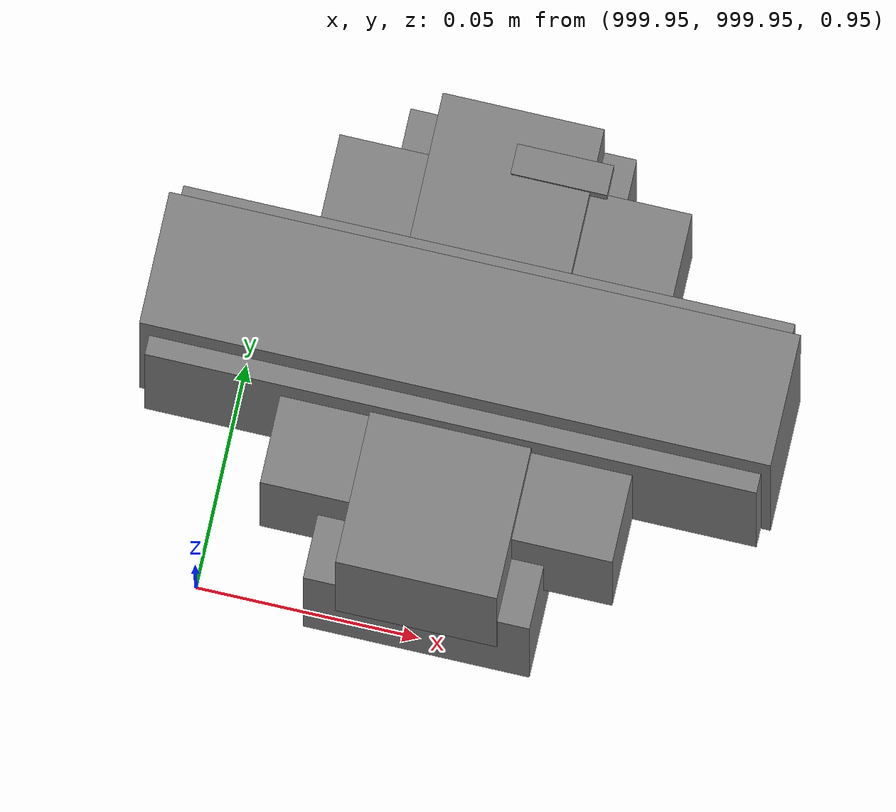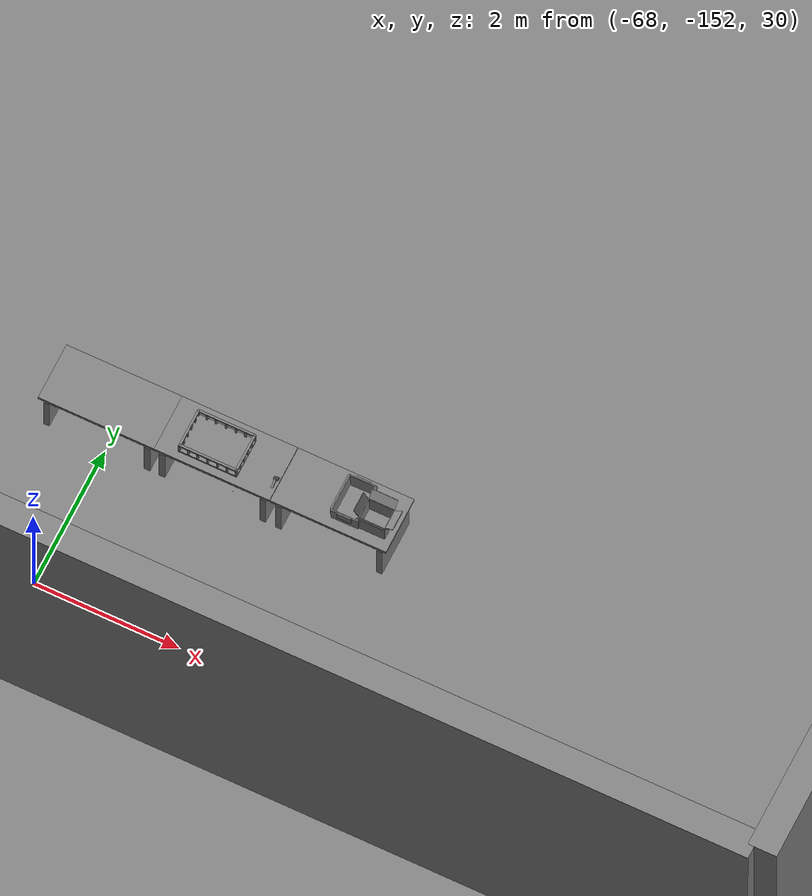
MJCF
<mujoco>
    <option gravity="0.000000000 0.000000000 -9.810000420" timestep="0.0049999999" integrator="implicitfast" density="1.225" viscosity="1.8000001e-05" noslip_iterations="10" iterations="100" sdf_iterations="50">
        <flag multiccd="disable"/>
    </option>
    <size memory="1000M"/>
    <compiler coordinate="local"/>
    <worldbody>
        <light cutoff="30" pos="0 1 1" dir="0 -1 -2"/>
        <light cutoff="30" pos="0 -1 1" dir="0 1 -2"/>
        <body pos="-64.866622925 -149.383972168 30.183746338" euler="89.999984741 89.999946594 0.000000000" name="openloong_gripper_2f85_fix_base_usda_bluebox_01">
            <geom contype="1" conaffinity="1" density="1000" type="box" material="" rgba="0.500000000 0.500000000 0.500000000 1.000000000" solimp="0.899999976 0.949999988 0.001000000" friction="1.000000000 0.005000000 0.000100000" solref="0.020000000 1.000000000" margin="0" condim="3" group="0" pos="0.276580811 0.187225342 0.000068665" quat="0.707106948 0.000077471 0.707106352 0.000077486" size="0.100000001 0.057999998 0.010000000" name="openloong_gripper_2f85_fix_base_usda_geom_9F6DDFC6_DA82_424C_8C21_CB474DA22678"/>
            <geom contype="1" conaffinity="1" density="1000" type="box" material="" rgba="0.500000000 0.500000000 0.500000000 1.000000000" solimp="0.899999976 0.949999988 0.001000000" friction="1.000000000 0.005000000 0.000100000" solref="0.020000000 1.000000000" margin="0" condim="3" group="0" pos="0.000000000 0.002883911 0.000000000" quat="0.999999881 0.000000000 0.000000000 0.000000000" size="0.254000008 0.003000000 0.172000006" name="openloong_gripper_2f85_fix_base_usda_geom_57432B26_BD2A_4586_B918_414E8260082C"/>
            <geom contype="1" conaffinity="1" density="1000" type="box" material="" rgba="0.500000000 0.500000000 0.500000000 1.000000000" solimp="0.899999976 0.949999988 0.001000000" friction="1.000000000 0.005000000 0.000100000" solref="0.020000000 1.000000000" margin="0" condim="3" group="0" pos="0.000000000 0.124874115 0.173484802" quat="0.999796331 0.020176515 -0.000000015 0.000000030" size="0.259999990 0.119999997 0.007000000" name="openloong_gripper_2f85_fix_base_usda_geom_85246B7B_5C4B_40ED_8E42_AC74BF64571A"/>
            <geom contype="1" conaffinity="1" density="1000" type="box" material="" rgba="0.500000000 0.500000000 0.500000000 1.000000000" solimp="0.899999976 0.949999988 0.001000000" friction="1.000000000 0.005000000 0.000100000" solref="0.020000000 1.000000000" margin="0" condim="3" group="0" pos="0.000000000 0.124874115 -0.173469543" quat="0.999796331 -0.020176545 -0.000000015 0.000000000" size="0.259999990 0.119999997 0.007000000" name="openloong_gripper_2f85_fix_base_usda_geom_25851209_FC08_4766_97D6_C43D230D404A"/>
            <geom contype="1" conaffinity="1" density="1000" type="box" material="" rgba="0.500000000 0.500000000 0.500000000 1.000000000" solimp="0.899999976 0.949999988 0.001000000" friction="1.000000000 0.005000000 0.000100000" solref="0.020000000 1.000000000" margin="0" condim="3" group="0" pos="0.000000000 0.214008331 0.188980103" quat="0.999912977 0.013176724 0.000000015 0.000000000" size="0.259999990 0.029999999 0.012500000" name="openloong_gripper_2f85_fix_base_usda_geom_63C9AC0F_82A6_4F72_B022_B41A7ABC633E"/>
            <geom contype="1" conaffinity="1" density="1000" type="box" material="" rgba="0.500000000 0.500000000 0.500000000 1.000000000" solimp="0.899999976 0.949999988 0.001000000" friction="1.000000000 0.005000000 0.000100000" solref="0.020000000 1.000000000" margin="0" condim="3" group="0" pos="-0.258361816 0.125289917 0.001876831" quat="0.702796936 -0.020792112 0.710783124 0.020769298" size="0.189999998 0.119999997 0.009000000" name="openloong_gripper_2f85_fix_base_usda_geom_B8DB2C95_8322_46AD_AD0C_513BA57BB1B8"/>
            <geom contype="1" conaffinity="1" density="1000" type="box" material="" rgba="0.500000000 0.500000000 0.500000000 1.000000000" solimp="0.899999976 0.949999988 0.001000000" friction="1.000000000 0.005000000 0.000100000" solref="0.020000000 1.000000000" margin="0" condim="3" group="0" pos="0.000000000 0.214008331 -0.188980103" quat="0.999912977 -0.013176769 0.000000030 0.000000015" size="0.259999990 0.029999999 0.012500000" name="openloong_gripper_2f85_fix_base_usda_geom_43136DEE_6F30_40B6_AA06_A62ECF7A489A"/>
            <geom contype="1" conaffinity="1" density="1000" type="box" material="" rgba="0.500000000 0.500000000 0.500000000 1.000000000" solimp="0.899999976 0.949999988 0.001000000" friction="1.000000000 0.005000000 0.000100000" solref="0.020000000 1.000000000" margin="0" condim="3" group="0" pos="-0.276611328 0.187225342 0.000068665" quat="0.707106650 0.000077441 0.707106709 0.000077456" size="0.100000001 0.057999998 0.010000000" name="openloong_gripper_2f85_fix_base_usda_geom_D78EAEE7_39C0_403C_8BBC_EF40D8F9F043"/>
            <geom contype="1" conaffinity="1" density="1000" type="box" material="" rgba="0.500000000 0.500000000 0.500000000 1.000000000" solimp="0.899999976 0.949999988 0.001000000" friction="1.000000000 0.005000000 0.000100000" solref="0.020000000 1.000000000" margin="0" condim="3" group="0" pos="0.258331299 0.125289917 0.001876831" quat="0.702851415 0.018856421 0.710823774 -0.019329369" size="0.189999998 0.119999997 0.009000000" name="openloong_gripper_2f85_fix_base_usda_geom_EBBCE5BF_6E61_4FE1_A87D_7505C3D659CD"/>
            <freejoint name="openloong_gripper_2f85_fix_base_usda_bluebox_01_joint"/>
            <site size="0.005000000 0.005000000 0.005000000" rgba="0.500000000 0.500000000 0.500000000 1.000000000" pos="0.000000000 0.000000000 0.000000000" quat="0.999961913 0.008726534 0.000000000 0.000000000" group="0" type="sphere" name="openloong_gripper_2f85_fix_base_usda_bluebox_01site"/>
        </body>
        <body pos="-64.496299744 -149.491867065 30.235729218" euler="0.000000000 0.000000000 89.999946594" name="openloong_gripper_2f85_fix_base_usda_cardboardbox_01">
            <geom contype="1" conaffinity="1" density="1000" type="box" material="" rgba="0.500000000 0.500000000 0.500000000 1.000000000" solimp="0.899999976 0.949999988 0.001000000" friction="1.000000000 0.005000000 0.000100000" solref="0.020000000 1.000000000" margin="0" condim="3" group="0" pos="-0.003166199 -0.004086494 0.005052090" quat="1.000000000 0.000000000 0.000000000 0.000000000" size="0.142499998 0.177500010 0.005000000" name="openloong_gripper_2f85_fix_base_usda_geom_A5CF9FDF_22C2_431A_844A_9FF615A55C40"/>
            <geom contype="1" conaffinity="1" density="1000" type="box" material="" rgba="0.500000000 0.500000000 0.500000000 1.000000000" solimp="0.899999976 0.949999988 0.001000000" friction="1.000000000 0.005000000 0.000100000" solref="0.020000000 1.000000000" margin="0" condim="3" group="0" pos="-0.003166199 0.170316696 0.150570869" quat="1.000000000 0.000000000 0.000000000 0.000000000" size="0.142499998 0.005000000 0.149999991" name="openloong_gripper_2f85_fix_base_usda_geom_9918E471_6DC9_4B70_9F16_B04EF882744C"/>
            <geom contype="1" conaffinity="1" density="1000" type="box" material="" rgba="0.500000000 0.500000000 0.500000000 1.000000000" solimp="0.899999976 0.949999988 0.001000000" friction="1.000000000 0.005000000 0.000100000" solref="0.020000000 1.000000000" margin="0" condim="3" group="0" pos="-0.147399902 -0.005307198 0.150570869" quat="1.000000000 0.000000000 0.000000000 0.000000000" size="0.005000000 0.177500010 0.149999991" name="openloong_gripper_2f85_fix_base_usda_geom_BDA6F463_2B98_4642_B3EB_CD5576BD3E0F"/>
            <geom contype="1" conaffinity="1" density="1000" type="box" material="" rgba="0.500000000 0.500000000 0.500000000 1.000000000" solimp="0.899999976 0.949999988 0.001000000" friction="1.000000000 0.005000000 0.000100000" solref="0.020000000 1.000000000" margin="0" condim="3" group="0" pos="0.140275955 -0.005307198 0.150570869" quat="1.000000000 0.000000000 0.000000000 0.000000000" size="0.005000000 0.177500010 0.149999991" name="openloong_gripper_2f85_fix_base_usda_geom_B281E148_F0DD_41E8_84F2_7AB37D3CA11B"/>
            <geom contype="1" conaffinity="1" density="1000" type="box" material="" rgba="0.500000000 0.500000000 0.500000000 1.000000000" solimp="0.899999976 0.949999988 0.001000000" friction="1.000000000 0.005000000 0.000100000" solref="0.020000000 1.000000000" margin="0" condim="3" group="0" pos="-0.003166199 -0.181550980 0.150570869" quat="1.000000000 0.000000000 0.000000000 0.000000000" size="0.142499998 0.005000000 0.149999991" name="openloong_gripper_2f85_fix_base_usda_geom_34CF1B34_FF48_46F7_A7D2_6A3F1ED7233C"/>
            <freejoint name="openloong_gripper_2f85_fix_base_usda_cardboardbox_01_joint"/>
            <site size="0.005000000 0.005000000 0.005000000" rgba="0.500000000 0.500000000 0.500000000 1.000000000" pos="0.000000000 0.000000000 0.000000000" quat="0.999961913 0.008726535 0.000000000 0.000000000" group="0" type="sphere" name="openloong_gripper_2f85_fix_base_usda_site_70A359E7_D911_409C_BE82_806D7F90880A"/>
            <body pos="0.139160156 -0.004048347 0.301930904" euler="-179.999954224 49.383502960 179.999954224" name="openloong_gripper_2f85_fix_base_usda_A1_006">
                <geom contype="1" conaffinity="1" density="1000" type="box" material="" rgba="0.500000000 0.500000000 0.500000000 1.000000000" solimp="0.899999976 0.949999988 0.001000000" friction="1.000000000 0.005000000 0.000100000" solref="0.020000000 1.000000000" margin="0" condim="3" group="0" pos="-0.071587563 0.000009537 0.001745224" quat="0.999999881 0.000000000 0.000000000 0.000000000" size="0.071249999 0.179999992 0.002500000" name="openloong_gripper_2f85_fix_base_usda_geom_6061A515_F4F8_4D50_8C87_3E6C87EEA553"/>
                <joint armature="0" stiffness="0.07" damping="0.0099999998" axis="0.000000 1.000000 0.000000" type="hinge" name="openloong_gripper_2f85_fix_base_usda_A1_006"/>
            </body>
            <body pos="-0.145902634 -0.004086494 0.301938057" euler="-180.000000000 -60.000011444 -180.000000000" name="openloong_gripper_2f85_fix_base_usda_A2_006">
                <geom contype="1" conaffinity="1" density="1000" type="box" material="" rgba="0.500000000 0.500000000 0.500000000 1.000000000" solimp="0.899999976 0.949999988 0.001000000" friction="1.000000000 0.005000000 0.000100000" solref="0.020000000 1.000000000" margin="0" condim="3" group="0" pos="0.071268082 0.000009537 0.002717972" quat="0.000002921 0.000000000 -0.000000030 0.999999881" size="0.071249999 0.179999992 0.002500000" name="openloong_gripper_2f85_fix_base_usda_geom_43175928_714F_475A_AA36_4C6B1A08216C"/>
                <joint armature="0" stiffness="0.07" damping="0.0099999998" axis="0.000000 1.000000 0.000000" type="hinge" name="openloong_gripper_2f85_fix_base_usda_A2_006"/>
            </body>
            <body pos="-0.003385544 0.175991058 0.301930904" euler="-125.858116150 -0.000004561 0.000002331" name="openloong_gripper_2f85_fix_base_usda_B2_006">
                <geom contype="1" conaffinity="1" density="1000" type="box" material="" rgba="0.500000000 0.500000000 0.500000000 1.000000000" solimp="0.899999976 0.949999988 0.001000000" friction="1.000000000 0.005000000 0.000100000" solref="0.020000000 1.000000000" margin="0" condim="3" group="0" pos="0.000009537 -0.070939064 -0.002470016" quat="0.999614120 0.027776197 -0.000000015 0.000000030" size="0.137500003 0.064999998 0.005000000" name="openloong_gripper_2f85_fix_base_usda_geom_5C0C4BED_BD81_4588_A3BF_2BBE42E821E4"/>
                <joint armature="0" stiffness="0.07" damping="0.0099999998" axis="1.000000 0.000000 0.000000" type="hinge" name="openloong_gripper_2f85_fix_base_usda_B2_006"/>
            </body>
            <body pos="-0.003385544 -0.184140205 0.301938057" euler="147.805557251 0.000000000 0.000000000" name="openloong_gripper_2f85_fix_base_usda_B1_006">
                <geom contype="1" conaffinity="1" density="1000" type="box" material="" rgba="0.500000000 0.500000000 0.500000000 1.000000000" solimp="0.899999976 0.949999988 0.001000000" friction="1.000000000 0.005000000 0.000100000" solref="0.020000000 1.000000000" margin="0" condim="3" group="0" pos="-0.000028610 0.070202351 -0.002703667" quat="0.999614179 -0.027776167 0.000000000 0.000000000" size="0.137500003 0.064999998 0.005000000" name="openloong_gripper_2f85_fix_base_usda_geom_109424BC_728F_4A18_AFF6_D6086B7A8C18"/>
                <joint armature="0" stiffness="0.07" damping="0.0099999998" axis="1.000000 0.000000 0.000000" type="hinge" name="openloong_gripper_2f85_fix_base_usda_B1_006"/>
            </body>
        </body>
        <body pos="-65.882858276 -149.481979370 30.229999542" euler="-64.487716675 0.000000000 0.000000000" name="openloong_gripper_2f85_fix_base_usda_Barcode">
            <geom contype="1" conaffinity="1" density="1000" type="box" material="" rgba="0.500000000 0.500000000 0.500000000 1.000000000" solimp="0.899999976 0.949999988 0.001000000" friction="1.000000000 0.005000000 0.000100000" solref="0.020000000 1.000000000" margin="0" condim="3" group="0" pos="0.000000000 0.013038635 0.001419067" quat="0.000000000 0.000000000 0.000000000 1.000000119" size="0.034000002 0.010000000 0.017999999" name="openloong_gripper_2f85_fix_base_usda_geom_21A0E98B_E34A_45DB_BD56_28331D0A1253"/>
            <geom contype="1" conaffinity="1" density="1000" type="box" material="" rgba="0.500000000 0.500000000 0.500000000 1.000000000" solimp="0.899999976 0.949999988 0.001000000" friction="1.000000000 0.005000000 0.000100000" solref="0.020000000 1.000000000" margin="0" condim="3" group="0" pos="0.000000000 -0.035301208 -0.007095337" quat="0.000000000 0.000000000 -0.043619365 0.999048233" size="0.028999999 0.010000000 0.020000000" name="openloong_gripper_2f85_fix_base_usda_geom_9E8934AA_5D3D_4A64_BA48_3791534EB61F"/>
            <geom contype="1" conaffinity="1" density="1000" type="box" material="" rgba="0.500000000 0.500000000 0.500000000 1.000000000" solimp="0.899999976 0.949999988 0.001000000" friction="1.000000000 0.005000000 0.000100000" solref="0.020000000 1.000000000" margin="0" condim="3" group="0" pos="0.000000000 -0.043411255 -0.011749268" quat="0.922262907 0.386563420 0.000000000 0.000000000" size="0.026000001 0.010000000 0.020000000" name="openloong_gripper_2f85_fix_base_usda_geom_F406F84E_E161_439A_85F2_00B42CE2A909"/>
            <geom contype="1" conaffinity="1" density="1000" type="box" material="" rgba="0.500000000 0.500000000 0.500000000 1.000000000" solimp="0.899999976 0.949999988 0.001000000" friction="1.000000000 0.005000000 0.000100000" solref="0.020000000 1.000000000" margin="0" condim="3" group="0" pos="0.000000000 -0.016967773 -0.031860352" quat="0.000000000 0.000000000 0.000000000 1.000000119" size="0.008000000 0.010000000 0.013000000" name="openloong_gripper_2f85_fix_base_usda_geom_49AF1AFD_8641_4616_BC51_FDFD796152B2"/>
            <geom contype="1" conaffinity="1" density="1000" type="box" material="" rgba="0.500000000 0.500000000 0.500000000 1.000000000" solimp="0.899999976 0.949999988 0.001000000" friction="1.000000000 0.005000000 0.000100000" solref="0.020000000 1.000000000" margin="0" condim="3" group="0" pos="0.000000000 -0.001869202 0.000312805" quat="0.953716993 0.300705761 0.000000000 0.000000000" size="0.032000002 0.010000000 0.018999999" name="openloong_gripper_2f85_fix_base_usda_geom_1F112EBE_64D5_44BC_B58D_6B9107677ACC"/>
            <geom contype="1" conaffinity="1" density="1000" type="box" material="" rgba="0.500000000 0.500000000 0.500000000 1.000000000" solimp="0.899999976 0.949999988 0.001000000" friction="1.000000000 0.005000000 0.000100000" solref="0.020000000 1.000000000" margin="0" condim="3" group="0" pos="0.000000000 -0.019531250 -0.003173828" quat="0.953716993 0.300705761 0.000000000 0.000000000" size="0.030999999 0.010000000 0.020000000" name="openloong_gripper_2f85_fix_base_usda_geom_B6D23327_1E9F_440F_9B3F_E7F1F27F132F"/>
            <geom contype="1" conaffinity="1" density="1000" type="box" material="" rgba="0.500000000 0.500000000 0.500000000 1.000000000" solimp="0.899999976 0.949999988 0.001000000" friction="1.000000000 0.005000000 0.000100000" solref="0.020000000 1.000000000" margin="0" condim="3" group="0" pos="0.000000000 -0.035301208 -0.007095337" quat="0.953716993 0.300705761 0.000000000 0.000000000" size="0.028999999 0.010000000 0.020000000" name="openloong_gripper_2f85_fix_base_usda_geom_25724E4E_12AE_46EA_A67D_2728161223D1"/>
            <geom contype="1" conaffinity="1" density="1000" type="box" material="" rgba="0.500000000 0.500000000 0.500000000 1.000000000" solimp="0.899999976 0.949999988 0.001000000" friction="1.000000000 0.005000000 0.000100000" solref="0.020000000 1.000000000" margin="0" condim="3" group="0" pos="0.000000000 -0.042617798 -0.071121216" quat="0.000000000 0.000000000 0.000000000 1.000000119" size="0.013000000 0.021000000 0.059999999" name="openloong_gripper_2f85_fix_base_usda_geom_806F5215_6C32_4DF8_AC2D_E6478619B1D5"/>
            <freejoint name="openloong_gripper_2f85_fix_base_usda_Barcode_joint"/>
            <site size="0.005000000 0.005000000 0.005000000" rgba="0.500000000 0.500000000 0.500000000 1.000000000" pos="0.000000000 0.000000000 0.000000000" quat="1.000000000 0.000000000 0.000000000 0.000000000" group="0" type="sphere" name="openloong_gripper_2f85_fix_base_usda_Barcode_site"/>
        </body>
        <body pos="-66.745018005 -149.392349243 30.184000015" euler="0.000000000 0.000000000 89.999946594" name="[22332776753363]_Basket_01">
            <geom contype="1" conaffinity="1" density="1000" type="box" material="" rgba="0.500000000 0.500000000 0.500000000 1.000000000" solimp="0.899999976 0.949999988 0.001000000" friction="1.000000000 0.005000000 0.000100000" solref="0.020000000 1.000000000" margin="0" condim="3" group="0" pos="-0.052425385 0.389207840 0.089787483" quat="0.707107008 0.000000000 0.000000000 0.707106411" size="0.014249999 0.014249999 0.059999999" name="[22332776753363]_geom_EB3D7371_5C69_43DA_BCB8_0B6934EF440C"/>
            <geom contype="1" conaffinity="1" density="1000" type="box" material="" rgba="0.500000000 0.500000000 0.500000000 1.000000000" solimp="0.899999976 0.949999988 0.001000000" friction="1.000000000 0.005000000 0.000100000" solref="0.020000000 1.000000000" margin="0" condim="3" group="0" pos="0.264015198 -0.133043289 0.089787483" quat="0.707107008 0.000000000 0.000000000 0.707106411" size="0.014249999 0.014249999 0.059999999" name="[22332776753363]_geom_D9AFDB40_6A18_4FF2_BE56_68A8FE9371E7"/>
            <geom contype="1" conaffinity="1" density="1000" type="box" material="" rgba="0.500000000 0.500000000 0.500000000 1.000000000" solimp="0.899999976 0.949999988 0.001000000" friction="1.000000000 0.005000000 0.000100000" solref="0.020000000 1.000000000" margin="0" condim="3" group="0" pos="-0.264015198 -0.265548706 0.089793205" quat="0.707107008 0.000000000 0.000000000 0.707106411" size="0.014249999 0.014249999 0.059999999" name="[22332776753363]_geom_A6536510_C1AD_44A8_9F29_15B6B380EB3E"/>
            <geom contype="1" conaffinity="1" density="1000" type="box" material="" rgba="0.500000000 0.500000000 0.500000000 1.000000000" solimp="0.899999976 0.949999988 0.001000000" friction="1.000000000 0.005000000 0.000100000" solref="0.020000000 1.000000000" margin="0" condim="3" group="0" pos="-0.160263062 -0.389322281 0.089793205" quat="0.707107008 0.000000000 0.000000000 0.707106411" size="0.014249999 0.014249999 0.059999999" name="[22332776753363]_geom_68203E6F_B9CE_4FD2_8063_9C1FF6A5ADE6"/>
            <geom contype="1" conaffinity="1" density="1000" type="box" material="" rgba="0.500000000 0.500000000 0.500000000 1.000000000" solimp="0.899999976 0.949999988 0.001000000" friction="1.000000000 0.005000000 0.000100000" solref="0.020000000 1.000000000" margin="0" condim="3" group="0" pos="0.162265778 -0.389322281 0.089787483" quat="0.707107008 0.000000000 0.000000000 0.707106411" size="0.014249999 0.014249999 0.059999999" name="[22332776753363]_geom_8D925037_4A9D_4C9B_B012_0A357A762682"/>
            <geom contype="1" conaffinity="1" density="1000" type="box" material="" rgba="0.500000000 0.500000000 0.500000000 1.000000000" solimp="0.899999976 0.949999988 0.001000000" friction="1.000000000 0.005000000 0.000100000" solref="0.020000000 1.000000000" margin="0" condim="3" group="0" pos="0.264015198 0.389207840 0.089787483" quat="0.707107008 0.000000000 0.000000000 0.707106411" size="0.014249999 0.014249999 0.059999999" name="[22332776753363]_geom_7CF31FF0_8680_48B0_B575_ED38EC6FDE0A"/>
            <geom contype="1" conaffinity="1" density="1000" type="box" material="" rgba="0.500000000 0.500000000 0.500000000 1.000000000" solimp="0.899999976 0.949999988 0.001000000" friction="1.000000000 0.005000000 0.000100000" solref="0.020000000 1.000000000" margin="0" condim="3" group="0" pos="-0.264015198 -0.133043289 0.089793205" quat="0.707107008 0.000000000 0.000000000 0.707106411" size="0.014249999 0.014249999 0.059999999" name="[22332776753363]_geom_E8CA5C73_90BF_484A_A2DE_04CA8193E991"/>
            <geom contype="1" conaffinity="1" density="1000" type="box" material="" rgba="0.500000000 0.500000000 0.500000000 1.000000000" solimp="0.899999976 0.949999988 0.001000000" friction="1.000000000 0.005000000 0.000100000" solref="0.020000000 1.000000000" margin="0" condim="3" group="0" pos="-0.264026642 0.269256592 0.089793205" quat="0.707107008 0.000000000 0.000000000 0.707106411" size="0.014249999 0.014249999 0.059999999" name="[22332776753363]_geom_7DC520E6_7820_426E_A124_3DAB49A5A1EC"/>
            <geom contype="1" conaffinity="1" density="1000" type="box" material="" rgba="0.500000000 0.500000000 0.500000000 1.000000000" solimp="0.899999976 0.949999988 0.001000000" friction="1.000000000 0.005000000 0.000100000" solref="0.020000000 1.000000000" margin="0" condim="3" group="0" pos="0.054462433 0.389207840 0.089787483" quat="0.707107008 0.000000000 0.000000000 0.707106411" size="0.014249999 0.014249999 0.059999999" name="[22332776753363]_geom_BED44344_C68F_4D3C_B7A1_BC718B23ECED"/>
            <geom contype="1" conaffinity="1" density="1000" type="box" material="" rgba="0.500000000 0.500000000 0.500000000 1.000000000" solimp="0.899999976 0.949999988 0.001000000" friction="1.000000000 0.005000000 0.000100000" solref="0.020000000 1.000000000" margin="0" condim="3" group="0" pos="0.054462433 -0.389322281 0.089787483" quat="0.707107008 0.000000000 0.000000000 0.707106411" size="0.014249999 0.014249999 0.059999999" name="[22332776753363]_geom_B25A5670_7589_4DF7_BBD7_5E562DFFFD67"/>
            <geom contype="1" conaffinity="1" density="1000" type="box" material="" rgba="0.500000000 0.500000000 0.500000000 1.000000000" solimp="0.899999976 0.949999988 0.001000000" friction="1.000000000 0.005000000 0.000100000" solref="0.020000000 1.000000000" margin="0" condim="3" group="0" pos="0.264015198 0.269256592 0.089793205" quat="0.707107008 0.000000000 0.000000000 0.707106411" size="0.014249999 0.014249999 0.059999999" name="[22332776753363]_geom_288CED3C_D876_44DB_ADCC_EBA42D6E354C"/>
            <geom contype="1" conaffinity="1" density="1000" type="box" material="" rgba="0.500000000 0.500000000 0.500000000 1.000000000" solimp="0.899999976 0.949999988 0.001000000" friction="1.000000000 0.005000000 0.000100000" solref="0.020000000 1.000000000" margin="0" condim="3" group="0" pos="0.264015198 -0.389322281 0.089787483" quat="0.707107008 0.000000000 0.000000000 0.707106411" size="0.014249999 0.014249999 0.059999999" name="[22332776753363]_geom_96B56343_823E_4DEC_9FE5_82F016153CD3"/>
            <geom contype="1" conaffinity="1" density="1000" type="box" material="" rgba="0.500000000 0.500000000 0.500000000 1.000000000" solimp="0.899999976 0.949999988 0.001000000" friction="1.000000000 0.005000000 0.000100000" solref="0.020000000 1.000000000" margin="0" condim="3" group="0" pos="0.000000000 0.000000000 0.015998840" quat="0.707107008 0.000000000 0.000000000 0.707106411" size="0.403499991 0.279000014 0.015750000" name="[22332776753363]_geom_89077D36_18F3_4CAB_8768_9474DCAEFE64"/>
            <geom contype="1" conaffinity="1" density="1000" type="box" material="" rgba="0.500000000 0.500000000 0.500000000 1.000000000" solimp="0.899999976 0.949999988 0.001000000" friction="1.000000000 0.005000000 0.000100000" solref="0.020000000 1.000000000" margin="0" condim="3" group="0" pos="0.000000000 -0.389476776 0.163619041" quat="0.707107008 0.000000000 0.000000000 0.707106411" size="0.015000000 0.277500004 0.015750000" name="[22332776753363]_geom_93BE5F74_E188_4C42_B2A7_3A82B9FE3EFE"/>
            <geom contype="1" conaffinity="1" density="1000" type="box" material="" rgba="0.500000000 0.500000000 0.500000000 1.000000000" solimp="0.899999976 0.949999988 0.001000000" friction="1.000000000 0.005000000 0.000100000" solref="0.020000000 1.000000000" margin="0" condim="3" group="0" pos="0.162265778 0.389207840 0.089787483" quat="0.707107008 0.000000000 0.000000000 0.707106411" size="0.014249999 0.014249999 0.059999999" name="[22332776753363]_geom_741EF47F_B98D_4F37_9B95_FFFF2B70AC21"/>
            <geom contype="1" conaffinity="1" density="1000" type="box" material="" rgba="0.500000000 0.500000000 0.500000000 1.000000000" solimp="0.899999976 0.949999988 0.001000000" friction="1.000000000 0.005000000 0.000100000" solref="0.020000000 1.000000000" margin="0" condim="3" group="0" pos="0.000000000 0.389471054 0.163619041" quat="0.707107008 0.000000000 0.000000000 0.707106411" size="0.015000000 0.277500004 0.015750000" name="[22332776753363]_geom_B0750A58_2836_4F06_BFB8_FD80DA817C5A"/>
            <geom contype="1" conaffinity="1" density="1000" type="box" material="" rgba="0.500000000 0.500000000 0.500000000 1.000000000" solimp="0.899999976 0.949999988 0.001000000" friction="1.000000000 0.005000000 0.000100000" solref="0.020000000 1.000000000" margin="0" condim="3" group="0" pos="-0.263511658 0.000000000 0.163619041" quat="0.707107008 0.000000000 0.000000000 0.707106411" size="0.403499991 0.015000000 0.015750000" name="[22332776753363]_geom_A68DE540_24DC_4351_90CF_DF6DF0AA2510"/>
            <geom contype="1" conaffinity="1" density="1000" type="box" material="" rgba="0.500000000 0.500000000 0.500000000 1.000000000" solimp="0.899999976 0.949999988 0.001000000" friction="1.000000000 0.005000000 0.000100000" solref="0.020000000 1.000000000" margin="0" condim="3" group="0" pos="-0.264015198 0.141334534 0.089793205" quat="0.707107008 0.000000000 0.000000000 0.707106411" size="0.014249999 0.014249999 0.059999999" name="[22332776753363]_geom_C6557CAD_2204_4426_9EB9_3FF25CD1035C"/>
            <geom contype="1" conaffinity="1" density="1000" type="box" material="" rgba="0.500000000 0.500000000 0.500000000 1.000000000" solimp="0.899999976 0.949999988 0.001000000" friction="1.000000000 0.005000000 0.000100000" solref="0.020000000 1.000000000" margin="0" condim="3" group="0" pos="0.264015198 -0.265548706 0.089787483" quat="0.707107008 0.000000000 0.000000000 0.707106411" size="0.014249999 0.014249999 0.059999999" name="[22332776753363]_geom_8776E059_775C_40A2_99A6_DADA03128922"/>
            <geom contype="1" conaffinity="1" density="1000" type="box" material="" rgba="0.500000000 0.500000000 0.500000000 1.000000000" solimp="0.899999976 0.949999988 0.001000000" friction="1.000000000 0.005000000 0.000100000" solref="0.020000000 1.000000000" margin="0" condim="3" group="0" pos="-0.160263062 0.389207840 0.089787483" quat="0.707107008 0.000000000 0.000000000 0.707106411" size="0.014249999 0.014249999 0.059999999" name="[22332776753363]_geom_9FF02902_0065_414D_80CA_B361F2D1CC11"/>
            <geom contype="1" conaffinity="1" density="1000" type="box" material="" rgba="0.500000000 0.500000000 0.500000000 1.000000000" solimp="0.899999976 0.949999988 0.001000000" friction="1.000000000 0.005000000 0.000100000" solref="0.020000000 1.000000000" margin="0" condim="3" group="0" pos="-0.052425385 -0.389322281 0.089787483" quat="0.707107008 0.000000000 0.000000000 0.707106411" size="0.014249999 0.014249999 0.059999999" name="[22332776753363]_geom_1CDDD701_F176_4380_9C54_2698E98B1B55"/>
            <geom contype="1" conaffinity="1" density="1000" type="box" material="" rgba="0.500000000 0.500000000 0.500000000 1.000000000" solimp="0.899999976 0.949999988 0.001000000" friction="1.000000000 0.005000000 0.000100000" solref="0.020000000 1.000000000" margin="0" condim="3" group="0" pos="-0.264026642 -0.389322281 0.089793205" quat="0.707107008 0.000000000 0.000000000 0.707106411" size="0.014249999 0.014249999 0.059999999" name="[22332776753363]_geom_87457372_1CB7_4163_BD44_78F154B22A97"/>
            <geom contype="1" conaffinity="1" density="1000" type="box" material="" rgba="0.500000000 0.500000000 0.500000000 1.000000000" solimp="0.899999976 0.949999988 0.001000000" friction="1.000000000 0.005000000 0.000100000" solref="0.020000000 1.000000000" margin="0" condim="3" group="0" pos="0.264015198 0.141334534 0.089787483" quat="0.707107008 0.000000000 0.000000000 0.707106411" size="0.014249999 0.014249999 0.059999999" name="[22332776753363]_geom_04B7C958_884B_484C_BE85_81891508036D"/>
            <geom contype="1" conaffinity="1" density="1000" type="box" material="" rgba="0.500000000 0.500000000 0.500000000 1.000000000" solimp="0.899999976 0.949999988 0.001000000" friction="1.000000000 0.005000000 0.000100000" solref="0.020000000 1.000000000" margin="0" condim="3" group="0" pos="-0.264015198 0.389207840 0.089793205" quat="0.707107008 0.000000000 0.000000000 0.707106411" size="0.014249999 0.014249999 0.059999999" name="[22332776753363]_geom_BF0149C5_1C2D_4C1D_AD03_7B58F28D0C81"/>
            <geom contype="1" conaffinity="1" density="1000" type="box" material="" rgba="0.500000000 0.500000000 0.500000000 1.000000000" solimp="0.899999976 0.949999988 0.001000000" friction="1.000000000 0.005000000 0.000100000" solref="0.020000000 1.000000000" margin="0" condim="3" group="0" pos="0.264015198 0.004480362 0.089787483" quat="0.707107008 0.000000000 0.000000000 0.707106411" size="0.014249999 0.014249999 0.059999999" name="[22332776753363]_geom_E8106895_5236_450B_B7AF_B5718E318BEF"/>
            <geom contype="1" conaffinity="1" density="1000" type="box" material="" rgba="0.500000000 0.500000000 0.500000000 1.000000000" solimp="0.899999976 0.949999988 0.001000000" friction="1.000000000 0.005000000 0.000100000" solref="0.020000000 1.000000000" margin="0" condim="3" group="0" pos="0.263694763 -0.000011444 0.163619041" quat="0.707107008 0.000000000 0.000000000 0.707106411" size="0.403499991 0.015000000 0.015750000" name="[22332776753363]_geom_AF1B252E_07C9_4B09_BD23_F336DAEFE1A5"/>
            <geom contype="1" conaffinity="1" density="1000" type="box" material="" rgba="0.500000000 0.500000000 0.500000000 1.000000000" solimp="0.899999976 0.949999988 0.001000000" friction="1.000000000 0.005000000 0.000100000" solref="0.020000000 1.000000000" margin="0" condim="3" group="0" pos="-0.264015198 0.004480362 0.089793205" quat="0.707107008 0.000000000 0.000000000 0.707106411" size="0.014249999 0.014249999 0.059999999" name="[22332776753363]_geom_26E6A7AF_31A9_4BAC_81F2_C81558E487F6"/>
            <freejoint name="[22332776753363]_joint_8F29CD64_1733_4F19_9A60_713A71F43702"/>
        </body>
        <body pos="0.000000000 0.000000000 0.000000000" euler="0.000000000 0.000000000 0.000000000" name="Static Objects_Static Objects">
            <geom contype="1" conaffinity="1" density="1000" type="box" material="" rgba="0.500000000 0.500000000 0.500000000 1.000000000" solimp="0.899999976 0.949999988 0.001000000" friction="1.000000000 0.005000000 0.000100000" solref="0.020000000 1.000000000" margin="0" condim="3" group="0" pos="-67.544113159 -149.365814209 29.727830887" quat="0.500000417 0.499999970 0.499999553 0.499999970" size="0.381000012 0.319999993 0.041000001" name="Static Objects_geom_1B14209E_CB74_4E8D_89BD_E2651F9564C5"/>
            <geom contype="1" conaffinity="1" density="1000" type="box" material="" rgba="0.500000000 0.500000000 0.500000000 1.000000000" solimp="0.899999976 0.949999988 0.001000000" friction="1.000000000 0.005000000 0.000100000" solref="0.020000000 1.000000000" margin="0" condim="3" group="0" pos="-68.239501953 -149.365814209 30.086868286" quat="0.500000417 0.499999970 0.499999553 0.499999970" size="0.370999992 0.039500002 0.745000005" name="Static Objects_geom_CA641311_E249_4543_9347_34ED21A0C7E9"/>
            <geom contype="1" conaffinity="1" density="1000" type="box" material="" rgba="0.500000000 0.500000000 0.500000000 1.000000000" solimp="0.899999976 0.949999988 0.001000000" friction="1.000000000 0.005000000 0.000100000" solref="0.020000000 1.000000000" margin="0" condim="3" group="0" pos="-68.239501953 -149.365814209 30.147235870" quat="0.500000417 0.499999970 0.499999553 0.499999970" size="0.400000006 0.022000000 0.800000012" name="Static Objects_geom_DDEA2E04_F498_42BB_8B26_86A2F33C8AD8"/>
            <geom contype="1" conaffinity="1" density="1000" type="box" material="" rgba="0.500000000 0.500000000 0.500000000 1.000000000" solimp="0.899999976 0.949999988 0.001000000" friction="1.000000000 0.005000000 0.000100000" solref="0.020000000 1.000000000" margin="0" condim="3" group="0" pos="-68.934890747 -149.365814209 29.727830887" quat="0.500000417 0.499999970 0.499999553 0.499999970" size="0.381000012 0.319999993 0.041000001" name="Static Objects_geom_89698DAB_5DA2_4DF6_922C_658AAC3D7ACA"/>
            <geom contype="1" conaffinity="1" density="1000" type="box" material="" rgba="0.500000000 0.500000000 0.500000000 1.000000000" solimp="0.899999976 0.949999988 0.001000000" friction="1.000000000 0.005000000 0.000100000" solref="0.020000000 1.000000000" margin="0" condim="3" group="0" pos="-68.239501953 -149.365814209 29.561563492" quat="0.500000417 0.499999970 0.499999553 0.499999970" size="0.020000000 0.022000000 0.660000026" name="Static Objects_geom_DB65E5E6_60BB_42FF_BE89_B6B4567E4403"/>
            <geom contype="1" conaffinity="1" density="1000" type="box" material="" rgba="0.500000000 0.500000000 0.500000000 1.000000000" solimp="0.899999976 0.949999988 0.001000000" friction="1.000000000 0.005000000 0.000100000" solref="0.020000000 1.000000000" margin="0" condim="3" group="0" pos="-65.945671082 -149.365814209 29.727830887" quat="0.500000417 0.499999970 0.499999553 0.499999970" size="0.381000012 0.319999993 0.041000001" name="Static Objects_geom_A7D3D8BD_0416_4F8B_AEA1_DF75CEFEBB42"/>
            <geom contype="1" conaffinity="1" density="1000" type="box" material="" rgba="0.500000000 0.500000000 0.500000000 1.000000000" solimp="0.899999976 0.949999988 0.001000000" friction="1.000000000 0.005000000 0.000100000" solref="0.020000000 1.000000000" margin="0" condim="3" group="0" pos="-66.641059875 -149.365814209 30.086868286" quat="0.500000417 0.499999970 0.499999553 0.499999970" size="0.370999992 0.039500002 0.745000005" name="Static Objects_geom_A06FEA45_1602_4008_BE92_D0125EB9199C"/>
            <geom contype="1" conaffinity="1" density="1000" type="box" material="" rgba="0.500000000 0.500000000 0.500000000 1.000000000" solimp="0.899999976 0.949999988 0.001000000" friction="1.000000000 0.005000000 0.000100000" solref="0.020000000 1.000000000" margin="0" condim="3" group="0" pos="-66.641059875 -149.365814209 30.147235870" quat="0.500000417 0.499999970 0.499999553 0.499999970" size="0.400000006 0.022000000 0.800000012" name="Static Objects_geom_36AB5393_1260_481C_9E4C_E48ECAAF6100"/>
            <geom contype="1" conaffinity="1" density="1000" type="box" material="" rgba="0.500000000 0.500000000 0.500000000 1.000000000" solimp="0.899999976 0.949999988 0.001000000" friction="1.000000000 0.005000000 0.000100000" solref="0.020000000 1.000000000" margin="0" condim="3" group="0" pos="-67.336448669 -149.365814209 29.727830887" quat="0.500000417 0.499999970 0.499999553 0.499999970" size="0.381000012 0.319999993 0.041000001" name="Static Objects_geom_F33041AC_34B9_49A6_98C8_B9D5B8AFD8BC"/>
            <geom contype="1" conaffinity="1" density="1000" type="box" material="" rgba="0.500000000 0.500000000 0.500000000 1.000000000" solimp="0.899999976 0.949999988 0.001000000" friction="1.000000000 0.005000000 0.000100000" solref="0.020000000 1.000000000" margin="0" condim="3" group="0" pos="-66.641059875 -149.365814209 29.561563492" quat="0.500000417 0.499999970 0.499999553 0.499999970" size="0.020000000 0.022000000 0.660000026" name="Static Objects_geom_28594CC6_09EE_4D0F_AB1D_C2747F8FB3F8"/>
            <geom contype="1" conaffinity="1" density="1000" type="box" material="" rgba="0.500000000 0.500000000 0.500000000 1.000000000" solimp="0.899999976 0.949999988 0.001000000" friction="1.000000000 0.005000000 0.000100000" solref="0.020000000 1.000000000" margin="0" condim="3" group="0" pos="-64.338577271 -149.365814209 29.727830887" quat="0.500000417 0.499999970 0.499999553 0.499999970" size="0.381000012 0.319999993 0.041000001" name="Static Objects_geom_1366C925_9FAD_452A_B27D_CBC993073A6D"/>
            <geom contype="1" conaffinity="1" density="1000" type="box" material="" rgba="0.500000000 0.500000000 0.500000000 1.000000000" solimp="0.899999976 0.949999988 0.001000000" friction="1.000000000 0.005000000 0.000100000" solref="0.020000000 1.000000000" margin="0" condim="3" group="0" pos="-65.033966064 -149.365814209 30.086868286" quat="0.500000417 0.499999970 0.499999553 0.499999970" size="0.370999992 0.039500002 0.745000005" name="Static Objects_geom_7486FF09_3A1F_40DE_9B85_E02ED4F1D05A"/>
            <geom contype="1" conaffinity="1" density="1000" type="box" material="" rgba="0.500000000 0.500000000 0.500000000 1.000000000" solimp="0.899999976 0.949999988 0.001000000" friction="1.000000000 0.005000000 0.000100000" solref="0.020000000 1.000000000" margin="0" condim="3" group="0" pos="-65.033966064 -149.365814209 30.147235870" quat="0.500000417 0.499999970 0.499999553 0.499999970" size="0.400000006 0.022000000 0.800000012" name="Static Objects_geom_B64E6ECD_E09C_43DA_B303_BD2EA5A09505"/>
            <geom contype="1" conaffinity="1" density="1000" type="box" material="" rgba="0.500000000 0.500000000 0.500000000 1.000000000" solimp="0.899999976 0.949999988 0.001000000" friction="1.000000000 0.005000000 0.000100000" solref="0.020000000 1.000000000" margin="0" condim="3" group="0" pos="-65.729354858 -149.365814209 29.727830887" quat="0.500000417 0.499999970 0.499999553 0.499999970" size="0.381000012 0.319999993 0.041000001" name="Static Objects_geom_40394D23_0DCF_4C12_A2BE_2E41F89346CE"/>
            <geom contype="1" conaffinity="1" density="1000" type="box" material="" rgba="0.500000000 0.500000000 0.500000000 1.000000000" solimp="0.899999976 0.949999988 0.001000000" friction="1.000000000 0.005000000 0.000100000" solref="0.020000000 1.000000000" margin="0" condim="3" group="0" pos="-65.033966064 -149.365814209 29.561563492" quat="0.500000417 0.499999970 0.499999553 0.499999970" size="0.020000000 0.022000000 0.660000026" name="Static Objects_geom_4D0022C6_F9BC_41E4_A42F_043E189DB0C0"/>
            <geom contype="1" conaffinity="1" density="1000" type="box" material="" rgba="0.500000000 0.500000000 0.500000000 1.000000000" solimp="0.899999976 0.949999988 0.001000000" friction="1.000000000 0.005000000 0.000100000" solref="0.020000000 1.000000000" margin="0" condim="3" group="0" pos="-61.754566193 -137.853729248 33.906845093" quat="0.707107067 0.000000000 0.000000000 0.707106471" size="0.759999990 0.759999990 4.500000000" name="Static Objects_geom_EED6C769_B60A_4E20_B7D8_2CC34CCA9FE9"/>
            <geom contype="1" conaffinity="1" density="1000" type="box" material="" rgba="0.500000000 0.500000000 0.500000000 1.000000000" solimp="0.899999976 0.949999988 0.001000000" friction="1.000000000 0.005000000 0.000100000" solref="0.020000000 1.000000000" margin="0" condim="3" group="0" pos="-57.511135101 -144.927108765 31.707921982" quat="1.000000000 0.000000000 0.000000000 0.000000000" size="0.200000003 8.000000000 2.299999952" name="Static Objects_geom_9EE025FE_9CC6_4E26_8460_B224A4749384"/>
            <geom contype="1" conaffinity="1" density="1000" type="box" material="" rgba="0.500000000 0.500000000 0.500000000 1.000000000" solimp="0.899999976 0.949999988 0.001000000" friction="1.000000000 0.005000000 0.000100000" solref="0.020000000 1.000000000" margin="0" condim="3" group="0" pos="-80.517646790 -157.574050903 31.688196182" quat="0.707107067 0.000000000 0.000000000 0.707106471" size="0.600000024 0.600000024 2.299999952" name="Static Objects_geom_A62FCE3B_5544_4D63_8FD6_36AB1A57B3B5"/>
            <geom contype="1" conaffinity="1" density="1000" type="box" material="" rgba="0.500000000 0.500000000 0.500000000 1.000000000" solimp="0.899999976 0.949999988 0.001000000" friction="1.000000000 0.005000000 0.000100000" solref="0.020000000 1.000000000" margin="0" condim="3" group="0" pos="-80.711044312 -147.414932251 31.666158676" quat="1.000000000 0.000000000 0.000000000 0.000000000" size="0.200000003 10.000000000 2.299999952" name="Static Objects_geom_E11C05E8_367F_4E1F_B70E_DBB5CBCFE2BD"/>
            <geom contype="1" conaffinity="1" density="1000" type="box" material="" rgba="0.500000000 0.500000000 0.500000000 1.000000000" solimp="0.899999976 0.949999988 0.001000000" friction="1.000000000 0.005000000 0.000100000" solref="0.020000000 1.000000000" margin="0" condim="3" group="0" pos="-57.687217712 -137.434692383 31.688196182" quat="0.707107067 0.000000000 0.000000000 0.707106471" size="0.600000024 0.600000024 2.299999952" name="Static Objects_geom_33195A71_1FB0_4F01_9594_EBB8B3B446D5"/>
            <geom contype="1" conaffinity="1" density="1000" type="box" material="" rgba="0.500000000 0.500000000 0.500000000 1.000000000" solimp="0.899999976 0.949999988 0.001000000" friction="1.000000000 0.005000000 0.000100000" solref="0.020000000 1.000000000" margin="0" condim="3" group="0" pos="-69.537033081 -140.263229370 31.714921951" quat="0.707107067 0.000000000 0.000000000 0.707106471" size="0.759999990 4.500000000 2.299999952" name="Static Objects_geom_1BE2731B_1098_47AF_88AE_B1A14C9FA08D"/>
            <geom contype="1" conaffinity="1" density="1000" type="box" material="" rgba="0.500000000 0.500000000 0.500000000 1.000000000" solimp="0.899999976 0.949999988 0.001000000" friction="1.000000000 0.005000000 0.000100000" solref="0.020000000 1.000000000" margin="0" condim="3" group="0" pos="-80.073638916 -137.853713989 33.906845093" quat="0.707107067 0.000000000 0.000000000 0.707106471" size="0.759999990 0.759999990 4.500000000" name="Static Objects_geom_07DA9991_78DF_4447_8EF1_D9F9D6076538"/>
            <geom contype="1" conaffinity="1" density="1000" type="box" material="" rgba="0.500000000 0.500000000 0.500000000 1.000000000" solimp="0.899999976 0.949999988 0.001000000" friction="1.000000000 0.005000000 0.000100000" solref="0.020000000 1.000000000" margin="0" condim="3" group="0" pos="-73.406707764 -155.734664917 31.707921982" quat="1.000000000 0.000000000 0.000000000 0.000000000" size="0.200000003 3.000000000 2.299999952" name="Static Objects_geom_CF50F014_9F12_4710_A5D8_E6A806A94D49"/>
            <geom contype="1" conaffinity="1" density="1000" type="box" material="" rgba="0.500000000 0.500000000 0.500000000 1.000000000" solimp="0.899999976 0.949999988 0.001000000" friction="1.000000000 0.005000000 0.000100000" solref="0.020000000 1.000000000" margin="0" condim="3" group="0" pos="-68.497543335 -137.448257446 31.707921982" quat="0.707107067 0.000000000 0.000000000 0.707106471" size="0.200000003 14.000000000 2.299999952" name="Static Objects_geom_C81EAA98_AB0E_44C9_8BDE_E27456AB4716"/>
            <geom contype="1" conaffinity="1" density="1000" type="cylinder" material="" rgba="0.500000000 0.500000000 0.500000000 1.000000000" solimp="0.899999976 0.949999988 0.001000000" friction="1.000000000 0.005000000 0.000100000" solref="0.020000000 1.000000000" margin="0" condim="3" group="0" pos="-68.868522644 -142.134506226 31.711090088" quat="0.707107067 0.000000000 0.000000000 0.707106471" size="0.509999990 2.299999952 1.000000000" name="Static Objects_geom_30531955_4ACE_47EA_A1F7_E00B7AFE1FF0"/>
            <geom contype="1" conaffinity="1" density="1000" type="plane" material="" rgba="0.500000000 0.500000000 0.500000000 1.000000000" solimp="0.899999976 0.949999988 0.001000000" friction="1.000000000 0.005000000 0.000100000" solref="0.020000000 1.000000000" margin="0" condim="3" group="0" pos="-72.873703003 -147.131927490 29.409669876" quat="1.000000000 0.000000000 0.000000000 0.000000000" size="18.000000000 14.000000000 1.000000000" name="Static Objects_geom_8B4C8264_3AD9_4F76_BDFB_D341263ABF21"/>
            <geom contype="1" conaffinity="1" density="1000" type="box" material="" rgba="0.500000000 0.500000000 0.500000000 1.000000000" solimp="0.899999976 0.949999988 0.001000000" friction="1.000000000 0.005000000 0.000100000" solref="0.020000000 1.000000000" margin="0" condim="3" group="0" pos="-79.943580627 -157.782272339 31.707921982" quat="0.707107067 0.000000000 0.000000000 0.707106471" size="0.200000003 7.000000000 2.299999952" name="Static Objects_geom_D3DAA4F1_42F9_4E95_8FE3_9DF7EF2517CD"/>
            <geom contype="1" conaffinity="1" density="1000" type="box" material="" rgba="0.500000000 0.500000000 0.500000000 1.000000000" solimp="0.899999976 0.949999988 0.001000000" friction="1.000000000 0.005000000 0.000100000" solref="0.020000000 1.000000000" margin="0" condim="3" group="0" pos="-65.421028137 -152.903442383 31.707921982" quat="0.707107067 0.000000000 0.000000000 0.707106471" size="0.200000003 7.800000191 2.299999952" name="Static Objects_geom_C1E7B404_B129_4BEE_A306_B5F08C4F078B"/>
            <geom contype="1" conaffinity="1" density="1000" type="box" material="" rgba="0.500000000 0.500000000 0.500000000 1.000000000" solimp="0.899999976 0.949999988 0.001000000" friction="1.000000000 0.005000000 0.000100000" solref="0.020000000 1.000000000" margin="0" condim="3" group="0" pos="-74.776908875 -149.964416504 31.688196182" quat="1.000000000 0.000000000 0.000000000 0.000000000" size="0.600000024 0.409999996 2.299999952" name="Static Objects_geom_3941178E_9A06_43F6_99A3_63370C5CC225"/>
            <geom contype="1" conaffinity="1" density="1000" type="cylinder" material="" rgba="0.500000000 0.500000000 0.500000000 1.000000000" solimp="0.899999976 0.949999988 0.001000000" friction="1.000000000 0.005000000 0.000100000" solref="0.020000000 1.000000000" margin="0" condim="3" group="0" pos="-60.161884308 -142.134506226 31.711090088" quat="0.707107067 0.000000000 0.000000000 0.707106471" size="0.509999990 2.299999952 1.000000000" name="Static Objects_geom_8A3741C0_3F35_4D12_9BAB_2A960A4F0833"/>
            <geom contype="1" conaffinity="1" density="1000" type="cylinder" material="" rgba="0.500000000 0.500000000 0.500000000 1.000000000" solimp="0.899999976 0.949999988 0.001000000" friction="1.000000000 0.005000000 0.000100000" solref="0.020000000 1.000000000" margin="0" condim="3" group="0" pos="-75.382453918 -149.963455200 31.711090088" quat="0.707107067 0.000000000 0.000000000 0.707106471" size="0.409999996 2.299999952 1.000000000" name="Static Objects_geom_D4E1921C_C017_4EE9_B689_9468DB5FC62B"/>
            <geom contype="1" conaffinity="1" density="1000" type="cylinder" material="" rgba="0.500000000 0.500000000 0.500000000 1.000000000" solimp="0.899999976 0.949999988 0.001000000" friction="1.000000000 0.005000000 0.000100000" solref="0.020000000 1.000000000" margin="0" condim="3" group="0" pos="-74.154960632 -149.963455200 31.711090088" quat="0.707107067 0.000000000 0.000000000 0.707106471" size="0.409999996 2.299999952 1.000000000" name="Static Objects_geom_304EE40F_9A50_4311_8C65_AC01602A5765"/>
            <geom contype="1" conaffinity="1" density="1000" type="cylinder" material="" rgba="0.500000000 0.500000000 0.500000000 1.000000000" solimp="0.899999976 0.949999988 0.001000000" friction="1.000000000 0.005000000 0.000100000" solref="0.020000000 1.000000000" margin="0" condim="3" group="0" pos="-77.566612244 -142.134506226 31.711090088" quat="0.707107067 0.000000000 0.000000000 0.707106471" size="0.509999990 2.299999952 1.000000000" name="Static Objects_geom_8C1BDF95_2F31_4FD9_81A6_8AA95DDB3256"/>
        </body>
        <body pos="-66.112113953 -149.408187866 31.171394348" euler="-105.114273071 86.943832397 174.257827759" mocap="true" name="spotlight1_SpotLight"/>
        <body pos="1000.000000000 999.999938965 1.000000000" euler="0.000000000 0.000000000 180.000000000" name="openloong_gripper_2f85_fix_base_usda_intelcore_i5">
            <geom contype="1" conaffinity="1" density="1000" type="box" material="" rgba="0.500000000 0.500000000 0.500000000 1.000000000" solimp="0.899999976 0.949999988 0.001000000" friction="1.000000000 0.005000000 0.000100000" solref="0.020000000 1.000000000" margin="0" condim="3" group="0" pos="0.000000000 0.000000000 0.051722717" quat="0.707106709 0.000000000 0.000000000 -0.707106769" size="0.052800000 0.018080002 0.052800000" name="openloong_gripper_2f85_fix_base_usda_geom_3D9B2BF8_3592_48D4_B89B_C46D9AE2B987"/>
            <freejoint name="openloong_gripper_2f85_fix_base_usda_intelcore_i5_joint"/>
            <site size="0.005000000 0.005000000 0.005000000" rgba="0.500000000 0.500000000 0.500000000 1.000000000" pos="0.000000000 0.000000000 0.000000000" quat="0.999961913 0.008726534 0.000000000 0.000000000" group="0" type="sphere" name="openloong_gripper_2f85_fix_base_usda_intelcore_i5site"/>
        </body>
        <body pos="-65.833015442 -149.145935059 31.171339035" euler="-79.428779602 -87.391242981 96.434234619" mocap="true" name="spotlight2_SpotLight"/>
        <body pos="1000.000000000 1000.000000000 1.000000000" euler="0.000011953 0.000005123 -179.999984741" name="openloong_gripper_2f85_fix_base_usda_intel_box">
            <geom contype="1" conaffinity="1" density="1000" type="box" material="" rgba="0.500000000 0.500000000 0.500000000 1.000000000" solimp="0.899999976 0.949999988 0.001000000" friction="1.000000000 0.005000000 0.000100000" solref="0.020000000 1.000000000" margin="0" condim="3" group="0" pos="0.000000000 -0.000067139 0.000082284" quat="0.707106709 0.000000225 0.000000253 0.707106650" size="0.052800003 0.025300000 0.052800003" name="openloong_gripper_2f85_fix_base_usda_geom_C2ECDB94_AC8E_4119_BCF7_5E4E33A743AE"/>
            <freejoint name="openloong_gripper_2f85_fix_base_usda_intel_box_joint"/>
            <site size="0.005000000 0.005000000 0.005000000" rgba="0.500000000 0.500000000 0.500000000 1.000000000" pos="0.000000000 0.000000000 0.000000000" quat="0.999961913 0.008726500 0.000000000 0.000000000" group="0" type="sphere" name="openloong_gripper_2f85_fix_base_usda_intel_boxsite"/>
        </body>
        <body pos="-66.277793884 -149.236999512 31.170162201" euler="14.710594177 81.840408325 -9.886259079" mocap="true" name="spotlight6_SpotLight"/>
        <body pos="1000.000000000 1000.000000000 1.000000000" euler="0.000000000 0.000000000 180.000000000" name="openloong_gripper_2f85_fix_base_usda_wifi_box">
            <geom contype="1" conaffinity="1" density="1000" type="box" material="" rgba="0.500000000 0.500000000 0.500000000 1.000000000" solimp="0.899999976 0.949999988 0.001000000" friction="1.000000000 0.005000000 0.000100000" solref="0.020000000 1.000000000" margin="0" condim="3" group="0" pos="0.000000000 0.000000000 0.058978677" quat="0.000000000 0.000000047 0.000000000 1.000000000" size="0.068499997 0.018999999 0.059000000" name="openloong_gripper_2f85_fix_base_usda_geom_3616EE65_00E9_4055_801E_1E4F57149305"/>
            <freejoint name="openloong_gripper_2f85_fix_base_usda_wifi_box_joint"/>
            <site size="0.005000000 0.005000000 0.005000000" rgba="0.500000000 0.500000000 0.500000000 1.000000000" pos="0.000000000 0.000000000 0.000000000" quat="0.999961913 0.008726500 0.000000000 0.000000000" group="0" type="sphere" name="openloong_gripper_2f85_fix_base_usda_wifi_boxsite"/>
        </body>
        <body pos="1000.000000000 1000.000000000 1.000000000" euler="0.000000000 0.000000000 180.000000000" name="openloong_gripper_2f85_fix_base_usda_cpu_fan">
            <geom contype="1" conaffinity="1" density="1000" type="box" material="" rgba="0.500000000 0.500000000 0.500000000 1.000000000" solimp="0.899999976 0.949999988 0.001000000" friction="1.000000000 0.005000000 0.000100000" solref="0.020000000 1.000000000" margin="0" condim="3" group="0" pos="0.000000000 0.000000000 0.070034981" quat="0.000000000 0.000000000 0.000000000 1.000000000" size="0.070700005 0.014699999 0.070700005" name="openloong_gripper_2f85_fix_base_usda_geom_3FF83D19_21C7_452B_99D4_E7286CBD3A07"/>
            <freejoint name="openloong_gripper_2f85_fix_base_usda_cpu_fan_joint"/>
            <site size="0.005000000 0.005000000 0.005000000" rgba="0.500000000 0.500000000 0.500000000 1.000000000" pos="0.000000000 0.000000000 0.000000000" quat="0.999961913 0.008726535 0.000000000 0.000000000" group="0" type="sphere" name="openloong_gripper_2f85_fix_base_usda_cpu_fancsite"/>
        </body>
        <body pos="1000.000000000 1000.000000000 1.000000000" euler="0.000000000 0.000000000 180.000000000" name="openloong_gripper_2f85_fix_base_usda_battery_01">
            <geom contype="1" conaffinity="1" density="1000" type="box" material="" rgba="0.500000000 0.500000000 0.500000000 1.000000000" solimp="0.899999976 0.949999988 0.001000000" friction="1.000000000 0.005000000 0.000100000" solref="0.020000000 1.000000000" margin="0" condim="3" group="0" pos="-0.011123657 -0.041940309 0.101691343" quat="1.000000000 0.000000000 0.000000000 0.000000000" size="0.010800000 0.003375000 0.004725000" name="openloong_gripper_2f85_fix_base_usda_geom_78E663CE_7430_4290_939D_CDA01DE6BDC6"/>
            <geom contype="1" conaffinity="1" density="1000" type="box" material="" rgba="0.500000000 0.500000000 0.500000000 1.000000000" solimp="0.899999976 0.949999988 0.001000000" friction="1.000000000 0.005000000 0.000100000" solref="0.020000000 1.000000000" margin="0" condim="3" group="0" pos="-0.010876465 -0.044247437 0.047066893" quat="0.998702705 -0.050920475 0.000000000 0.000000000" size="0.009450001 0.002700000 0.024975000" name="openloong_gripper_2f85_fix_base_usda_geom_00F95163_C271_44ED_962B_395463099034"/>
            <geom contype="1" conaffinity="1" density="1000" type="box" material="" rgba="0.500000000 0.500000000 0.500000000 1.000000000" solimp="0.899999976 0.949999988 0.001000000" friction="1.000000000 0.005000000 0.000100000" solref="0.020000000 1.000000000" margin="0" condim="3" group="0" pos="-0.001235962 -0.000659180 0.047381196" quat="1.000000000 0.000000000 0.000000000 0.000000000" size="0.039420001 0.039150000 0.047250003" name="openloong_gripper_2f85_fix_base_usda_geom_834F13EC_E811_4581_809F_19BD71C32B95"/>
            <geom contype="1" conaffinity="1" density="1000" type="box" material="" rgba="0.500000000 0.500000000 0.500000000 1.000000000" solimp="0.899999976 0.949999988 0.001000000" friction="1.000000000 0.005000000 0.000100000" solref="0.020000000 1.000000000" margin="0" condim="3" group="0" pos="-0.010876465 -0.039138794 0.009851727" quat="1.000000000 0.000000000 0.000000000 0.000000000" size="0.009450001 0.010800000 0.013500000" name="openloong_gripper_2f85_fix_base_usda_geom_2E7528B5_1EA3_4F6B_88C2_CB6C13B7EEDF"/>
            <geom contype="1" conaffinity="1" density="1000" type="box" material="" rgba="0.500000000 0.500000000 0.500000000 1.000000000" solimp="0.899999976 0.949999988 0.001000000" friction="1.000000000 0.005000000 0.000100000" solref="0.020000000 1.000000000" margin="0" condim="3" group="0" pos="-0.010876465 -0.041528322 0.071508206" quat="1.000000000 0.000000000 0.000000000 0.000000000" size="0.009450001 0.002700000 0.027000001" name="openloong_gripper_2f85_fix_base_usda_geom_9BE85851_AEA4_4C88_B99F_E1A6A78BE584"/>
            <freejoint name="openloong_gripper_2f85_fix_base_usda_battery_01_joint"/>
            <site size="0.005000000 0.005000000 0.005000000" rgba="0.500000000 0.500000000 0.500000000 1.000000000" pos="0.000000000 0.000000000 0.000000000" quat="0.999961913 0.008726500 0.000000000 0.000000000" group="0" type="sphere" name="openloong_gripper_2f85_fix_base_usda_battery_01site"/>
        </body>
        <body pos="-66.291030884 -149.869689941 29.018842697" euler="0.000000000 0.000000000 89.999946594" mocap="true" name="openloong_gripper_2f85_fix_base_usda_leftHandMocap"/>
        <body pos="-66.291030884 -149.869689941 29.018842697" euler="0.000000000 0.000000000 89.999946594" mocap="true" name="openloong_gripper_2f85_fix_base_usda_rightHandMocap"/>
        <body pos="-66.291030884 -149.869689941 30.218843460" euler="0.000000000 0.000000000 89.999946594" name="openloong_gripper_2f85_fix_base_usda_base_link">
            <geom contype="1" conaffinity="1" density="1000" type="mesh" material="" rgba="0.783999979 0.783999979 0.783999979 1.000000000" solimp="0.899999976 0.949999988 0.001000000" friction="1.000000000 0.005000000 0.000100000" solref="0.020000000 1.000000000" margin="0" condim="3" group="3" mesh="base_link" pos="0.000000000 0.000000000 0.000000000" quat="1.000000000 0.000000000 0.000000000 0.000000000" size="1.000000000 1.000000000 1.000000000" name="openloong_gripper_2f85_fix_base_usda__geom_7_03F48634_C689_44B8_84D9_1EABF169E102"/>
            <site size="0.005000000 0.005000000 0.005000000" rgba="0.500000000 0.500000000 0.500000000 1.000000000" pos="0.000000000 0.000000000 0.000000000" quat="1.000000000 0.000000000 0.000000000 0.000000000" group="0" type="sphere" name="openloong_gripper_2f85_fix_base_usda_imu"/>
            <inertial mass="22.447001" pos="-0.005664100 -0.001336700 0.238289997" diaginertia="0.374352545 0.277180195 0.220617250" quat="0.999247074 0.035235517 -0.015086859 0.006023135"/>
            <body pos="0.000000000 0.000000000 0.299997330" euler="0.000000000 0.000000000 0.000000000" name="openloong_gripper_2f85_fix_base_usda_dummy_body">
                <geom contype="1" conaffinity="1" density="1000" type="sphere" material="" rgba="0.783999979 0.783999979 0.783999979 1.000000000" solimp="0.899999976 0.949999988 0.001000000" friction="1.000000000 0.005000000 0.000100000" solref="0.020000000 1.000000000" margin="0" condim="3" group="3" pos="0.000000000 0.000000000 0.000000000" quat="1.000000000 0.000000000 0.000000000 0.000000000" size="0.010000000 0.000000000 0.000000000" name="openloong_gripper_2f85_fix_base_usda__geom_8_51553345_E12C_48E6_AB86_823DE000B258"/>
                <joint armature="0.0099999998" stiffness="0" damping="0.1" axis="0.000000 0.000000 1.000000" type="hinge" name="openloong_gripper_2f85_fix_base_usda_dummy_joint"/>
                <site size="0.010000000 0.005000000 0.005000000" rgba="0.500000000 0.500000000 0.500000000 1.000000000" pos="0.000000000 0.000000000 0.000000000" quat="1.000000000 0.000000000 0.000000000 0.000000000" group="3" type="sphere" name="openloong_gripper_2f85_fix_base_usda_dummy_site"/>
            </body>
            <body pos="0.009002686 0.000000000 0.406400681" euler="0.000000000 0.000000000 0.000000000" name="openloong_gripper_2f85_fix_base_usda_Link_head_yaw">
                <geom contype="1" conaffinity="1" density="1000" type="mesh" material="" rgba="0.783999979 0.783999979 0.783999979 1.000000000" solimp="0.899999976 0.949999988 0.001000000" friction="1.000000000 0.005000000 0.000100000" solref="0.020000000 1.000000000" margin="0" condim="3" group="3" mesh="Link_head_yaw" pos="0.000000000 0.000000000 0.000000000" quat="1.000000000 0.000000000 0.000000000 0.000000000" size="1.000000000 1.000000000 1.000000000" name="openloong_gripper_2f85_fix_base_usda__geom_10_8D875F85_54FB_48AE_B6ED_18EAB9186998"/>
                <inertial mass="0.84249002" pos="0.000000000 -0.002081400 0.044801001" diaginertia="0.000700588 0.000629000 0.000553812" quat="0.706933022 -0.015675601 0.015677100 0.706933022"/>
                <body pos="0.000000000 -0.034599304 0.048500061" euler="0.000000000 0.000000000 0.000000000" name="openloong_gripper_2f85_fix_base_usda_Link_head_pitch">
                    <geom contype="1" conaffinity="1" density="1000" type="mesh" material="" rgba="0.783999979 0.783999979 0.783999979 1.000000000" solimp="0.899999976 0.949999988 0.001000000" friction="1.000000000 0.005000000 0.000100000" solref="0.020000000 1.000000000" margin="0" condim="3" group="3" mesh="Link_head_pitch" pos="0.000000000 0.000000000 0.000000000" quat="1.000000000 0.000000000 0.000000000 0.000000000" size="1.000000000 1.000000000 1.000000000" name="openloong_gripper_2f85_fix_base_usda__geom_12_A34E1413_1C09_4D3E_AC8F_FA7C2913C669"/>
                    <inertial mass="1.3943" pos="0.020569000 0.033004001 0.125000000" diaginertia="0.006381400 0.006289940 0.004481460" quat="0.973390222 0.008406822 0.228157058 0.019624906"/>
                    <body pos="0.000000000 0.029998779 0.000000000" euler="0.000000000 0.000000000 0.000000000" name="openloong_gripper_2f85_fix_base_usda_neck_center_body">
                        <site size="0.010000000 0.005000000 0.005000000" rgba="0.500000000 0.500000000 0.500000000 1.000000000" pos="0.000000000 0.000000000 0.000000000" quat="1.000000000 0.000000000 0.000000000 0.000000000" group="3" type="sphere" name="openloong_gripper_2f85_fix_base_usda_neck_center_site"/>
                        <body pos="0.020004272 0.000000000 0.149999619" euler="-0.000002229 39.998176575 -90.000205994" name="openloong_gripper_2f85_fix_base_usda_camera_head">
                            <site size="0.010000000 0.005000000 0.005000000" rgba="0.500000000 0.500000000 0.500000000 1.000000000" pos="0.000000000 0.000000000 0.000000000" quat="1.000000000 0.000000000 0.000000000 0.000000000" group="3" type="sphere" name="openloong_gripper_2f85_fix_base_usda_camera_head_site"/>
                        </body>
                    </body>
                </body>
            </body>
            <body pos="0.003997803 -0.161598206 0.392200470" euler="0.000000000 0.000000000 0.000000000" name="openloong_gripper_2f85_fix_base_usda_Link_arm_r_01">
                <geom contype="1" conaffinity="1" density="1000" type="mesh" material="" rgba="0.783999979 0.783999979 0.783999979 1.000000000" solimp="0.899999976 0.949999988 0.001000000" friction="1.000000000 0.005000000 0.000100000" solref="0.020000000 1.000000000" margin="0" condim="3" group="3" mesh="Link_arm_r_01" pos="0.000000000 0.000000000 0.000000000" quat="1.000000000 0.000000000 0.000000000 0.000000000" size="1.000000000 1.000000000 1.000000000" name="openloong_gripper_2f85_fix_base_usda__geom_14_97F6D91E_CA5A_4C30_AD0A_47B40FBD4141"/>
                <joint armature="0.0099999998" stiffness="0" damping="1" axis="0.000000 -1.000000 0.000000" limited="true" range="-170.000015259 170.000015259" type="hinge" name="openloong_gripper_2f85_fix_base_usda_J_arm_r_01"/>
                <inertial mass="0.75641" pos="0.004494600 -0.038293999 -0.000001874" diaginertia="0.000842990 0.000803050 0.000587120" quat="-0.000163502 0.707098067 0.000812463 0.707115054"/>
                <body pos="-0.041992188 -0.041000366 0.000000000" euler="0.000000000 0.000000000 0.000000000" name="openloong_gripper_2f85_fix_base_usda_Link_arm_r_02">
                    <geom contype="1" conaffinity="1" density="1000" type="mesh" material="" rgba="0.783999979 0.783999979 0.783999979 1.000000000" solimp="0.899999976 0.949999988 0.001000000" friction="1.000000000 0.005000000 0.000100000" solref="0.020000000 1.000000000" margin="0" condim="3" group="3" mesh="Link_arm_r_02" pos="0.000000000 0.000000000 0.000000000" quat="1.000000000 0.000000000 0.000000000 0.000000000" size="1.000000000 1.000000000 1.000000000" name="openloong_gripper_2f85_fix_base_usda__geom_16_83A6A97E_7F9B_4BA5_85DF_74D8890EFBDC"/>
                    <joint armature="0.0099999998" stiffness="0" damping="1" axis="-1.000000 0.000000 0.000000" limited="true" range="-105.000244141 105.000244141" type="hinge" name="openloong_gripper_2f85_fix_base_usda_J_arm_r_02"/>
                    <inertial mass="0.98500001" pos="0.041999999 -0.067430697 0.000000000" diaginertia="0.002262690 0.001730990 0.001154020" quat="0.500000000 0.500000000 -0.500000000 0.500000000"/>
                    <body pos="0.041992188 -0.122596741 0.000000000" euler="0.000000000 0.000000000 0.000000000" name="openloong_gripper_2f85_fix_base_usda_Link_arm_r_03">
                        <geom contype="1" conaffinity="1" density="1000" type="mesh" material="" rgba="0.783999979 0.783999979 0.783999979 1.000000000" solimp="0.899999976 0.949999988 0.001000000" friction="1.000000000 0.005000000 0.000100000" solref="0.020000000 1.000000000" margin="0" condim="3" group="3" mesh="Link_arm_r_03" pos="0.000000000 0.000000000 0.000000000" quat="1.000000000 0.000000000 0.000000000 0.000000000" size="1.000000000 1.000000000 1.000000000" name="openloong_gripper_2f85_fix_base_usda__geom_18_CD8741E1_ED07_46C4_8FA0_C50076DDFACF"/>
                        <joint armature="0.0099999998" stiffness="0" damping="1" axis="0.000000 -1.000000 0.000000" limited="true" range="-170.000015259 170.000015259" type="hinge" name="openloong_gripper_2f85_fix_base_usda_J_arm_r_03"/>
                        <inertial mass="0.95899999" pos="-0.001413580 -0.164663002 0.020757901" diaginertia="0.002101340 0.002064590 0.000754802" quat="0.560480952 0.454391927 -0.443732947 0.531497955"/>
                        <body pos="0.035293579 -0.177406311 0.023998260" euler="0.000000000 0.000000000 0.000000000" name="openloong_gripper_2f85_fix_base_usda_Link_arm_r_04">
                            <geom contype="1" conaffinity="1" density="1000" type="mesh" material="" rgba="0.783999979 0.783999979 0.783999979 1.000000000" solimp="0.899999976 0.949999988 0.001000000" friction="1.000000000 0.005000000 0.000100000" solref="0.020000000 1.000000000" margin="0" condim="3" group="3" mesh="Link_arm_r_04" pos="0.000000000 0.000000000 0.000000000" quat="1.000000000 0.000000000 0.000000000 0.000000000" size="1.000000000 1.000000000 1.000000000" name="openloong_gripper_2f85_fix_base_usda__geom_20_88F59457_EAC2_47DC_94AC_7A09F7C9D2C9"/>
                            <joint armature="0.0099999998" stiffness="0" damping="1" axis="-1.000000 0.000000 0.000000" limited="true" range="0.000000000 170.000015259" type="hinge" name="openloong_gripper_2f85_fix_base_usda_J_arm_r_04"/>
                            <inertial mass="0.60000002" pos="-0.038727000 -0.060766999 -0.021003000" diaginertia="0.001092610 0.000712422 0.000645102" quat="0.327701002 0.632602990 -0.467366993 0.523443997"/>
                            <body pos="-0.035293579 -0.103492737 -0.023998260" euler="0.000000000 0.000000000 0.000000000" name="openloong_gripper_2f85_fix_base_usda_Link_arm_r_05">
                                <geom contype="1" conaffinity="1" density="1000" type="mesh" material="" rgba="0.783999979 0.783999979 0.783999979 1.000000000" solimp="0.899999976 0.949999988 0.001000000" friction="1.000000000 0.005000000 0.000100000" solref="0.020000000 1.000000000" margin="0" condim="3" group="3" mesh="Link_arm_r_05" pos="0.000000000 0.000000000 0.000000000" quat="1.000000000 0.000000000 0.000000000 0.000000000" size="1.000000000 1.000000000 1.000000000" name="openloong_gripper_2f85_fix_base_usda__geom_22_BE26C984_AF5C_4F63_9255_D227E8171032"/>
                                <joint armature="0.0099999998" stiffness="0" damping="1" axis="0.000000 -1.000000 0.000000" limited="true" range="-170.000015259 170.000015259" type="hinge" name="openloong_gripper_2f85_fix_base_usda_J_arm_r_05"/>
                                <inertial mass="0.68976003" pos="0.000032712 -0.068658002 -0.000111780" diaginertia="0.002522510 0.002411100 0.000448695" quat="0.707660973 0.706543028 -0.002603360 0.002470550"/>
                                <body pos="-0.026489258 -0.196502686 0.000000000" euler="0.000000000 0.000000000 0.000000000" name="openloong_gripper_2f85_fix_base_usda_Link_arm_r_06">
                                    <geom contype="1" conaffinity="1" density="1000" type="mesh" material="" rgba="0.783999979 0.783999979 0.783999979 1.000000000" solimp="0.899999976 0.949999988 0.001000000" friction="1.000000000 0.005000000 0.000100000" solref="0.020000000 1.000000000" margin="0" condim="3" group="3" mesh="Link_arm_r_06" pos="0.000000000 0.000000000 0.000000000" quat="1.000000000 0.000000000 0.000000000 0.000000000" size="1.000000000 1.000000000 1.000000000" name="openloong_gripper_2f85_fix_base_usda__geom_24_FFAE6A6A_4254_497E_9548_4A9C63AAE396"/>
                                    <joint armature="0.0099999998" stiffness="0" damping="1" axis="1.000000 0.000000 0.000000" limited="true" range="-105.000244141 105.000244141" type="hinge" name="openloong_gripper_2f85_fix_base_usda_J_arm_r_06"/>
                                    <inertial mass="0.28" pos="0.026078001 -0.000000896 0.001663700" diaginertia="0.000156930 0.000145601 0.000104979" quat="0.707080841 0.001851080 0.001883810 0.707127810"/>
                                    <body pos="0.026489258 0.000000000 0.031799316" euler="0.000000000 0.000000000 0.000000000" name="openloong_gripper_2f85_fix_base_usda_Link_arm_r_07">
                                        <geom contype="1" conaffinity="1" density="1000" type="mesh" material="" rgba="0.783999979 0.783999979 0.783999979 1.000000000" solimp="0.899999976 0.949999988 0.001000000" friction="1.000000000 0.005000000 0.000100000" solref="0.020000000 1.000000000" margin="0" condim="3" group="3" mesh="Link_arm_r_07" pos="0.000000000 0.000000000 0.000000000" quat="1.000000000 0.000000000 0.000000000 0.000000000" size="1.000000000 1.000000000 1.000000000" name="openloong_gripper_2f85_fix_base_usda__geom_26_A73D93C0_A38A_4859_89F5_37AEAD663C7F"/>
                                        <joint armature="0.0099999998" stiffness="0" damping="1" axis="0.000000 0.000000 1.000000" limited="true" range="-60.000133514 60.000133514" type="hinge" name="openloong_gripper_2f85_fix_base_usda_J_arm_r_07"/>
                                        <inertial mass="0.61353999" pos="-0.007859000 -0.158170000 -0.027736001" diaginertia="0.003037610 0.002570910 0.000729379" quat="0.427542925 0.443532884 -0.553093910 0.560867906"/>
                                        <body pos="0.000000000 0.286994934 -0.270000458" euler="150.000350952 -0.000001649 -0.000000442" name="openloong_gripper_2f85_fix_base_usda_camera_wrist_r">
                                            <site size="0.010000000 0.005000000 0.005000000" rgba="0.500000000 0.500000000 0.500000000 1.000000000" pos="0.000000000 0.000000000 0.000000000" quat="1.000000000 0.000000000 0.000000000 0.000000000" group="3" type="sphere" name="openloong_gripper_2f85_fix_base_usda_camera_wrist_r_site"/>
                                        </body>
                                        <body pos="0.000000000 -0.220008850 -0.033002853" euler="0.000000000 0.000000000 179.999969482" name="openloong_gripper_2f85_fix_base_usda_ee_center_body_r">
                                            <site size="0.010000000 0.005000000 0.005000000" rgba="0.500000000 0.500000000 0.500000000 1.000000000" pos="0.000000000 0.000000000 0.000000000" quat="1.000000000 0.000000000 0.000000000 0.000000000" group="3" type="sphere" name="openloong_gripper_2f85_fix_base_usda_ee_center_site_r"/>
                                        </body>
                                        <body pos="0.000000000 -0.066001892 -0.031000137" euler="89.999984741 0.000000000 180.000000000" name="openloong_gripper_2f85_fix_base_usda_zbr_base_link">
                                            <geom contype="1" conaffinity="1" density="1000" type="mesh" material="" rgba="0.783999979 0.783999979 0.783999979 1.000000000" solimp="0.899999976 0.949999988 0.001000000" friction="1.000000000 0.005000000 0.000100000" solref="0.020000000 1.000000000" margin="0" condim="3" group="3" mesh="base" pos="0.000000000 0.000003815 -0.000007629" quat="1.000000000 0.000000000 0.000000000 0.000000000" size="1.000000238 1.000000238 1.000000238" name="openloong_gripper_2f85_fix_base_usda__geom_30_05BF3C45_71FF_426B_A3A3_785BB559E260"/>
                                            <inertial mass="0.77744102" pos="0.000000000 -0.000027039 0.035467502" diaginertia="0.000260285 0.000225381 0.000152708" quat="0.999998808 -0.001528488 0.000000000 0.000000000"/>
                                            <body pos="-0.030609138 0.004745484 0.065696731" euler="-89.999984741 -0.000000000 0.000000000" name="openloong_gripper_2f85_fix_base_usda_r_left_driver">
                                                <geom contype="1" conaffinity="1" density="1000" type="mesh" material="" rgba="0.783999979 0.783999979 0.783999979 1.000000000" solimp="0.899999976 0.949999988 0.001000000" friction="1.000000000 0.005000000 0.000100000" solref="0.020000000 1.000000000" margin="0" condim="3" group="3" mesh="driver" pos="0.030609138 0.054901138 -0.004699708" quat="0.707106829 0.707106709 0.000000000 -0.000000000" size="1.000000238 1.000000238 1.000000238" name="openloong_gripper_2f85_fix_base_usda__geom_32_3B8601EE_742B_4BC9_ADE2_BF3A719A13CA"/>
                                                <joint armature="0.0049999999" stiffness="0" damping="0.1" axis="0.000000 0.000000 1.000000" limited="true" range="0.000000000 51.566200256" type="hinge" name="openloong_gripper_2f85_fix_base_usda_r_left_driver_joint"/>
                                                <inertial mass="0.0089956298" pos="0.000000000 0.017754700 0.001073140" diaginertia="0.000001724 0.000001609 0.000000322" quat="0.681301236 0.732003212 0.000000000 0.000000000"/>
                                                <body pos="-0.031402595 0.004524232 -0.010200503" euler="0.000000000 0.000000000 180.000000000" name="openloong_gripper_2f85_fix_base_usda_r_left_coupler">
                                                    <geom contype="1" conaffinity="1" density="1000" type="mesh" material="" rgba="0.783999979 0.783999979 0.783999979 1.000000000" solimp="0.899999976 0.949999988 0.001000000" friction="1.000000000 0.005000000 0.000100000" solref="0.020000000 1.000000000" margin="0" condim="3" group="3" mesh="coupler" pos="-0.062011734 -0.050354015 0.005500795" quat="0.707106829 -0.707106709 0.000000000 -0.000000000" size="1.000000238 1.000000238 1.000000238" name="openloong_gripper_2f85_fix_base_usda__geom_34_22569195_5D2D_4430_A38F_6687499CC649"/>
                                                    <inertial mass="0.0140974" pos="0.000000000 0.003012090 0.023217499" diaginertia="0.000004162 0.000003522 0.000000888" quat="0.705635548 -0.045590367 0.045590367 0.705635548"/>
                                                </body>
                                            </body>
                                            <body pos="-0.012695315 -0.012001040 0.072212234" euler="-89.999984741 -0.000000000 0.000000000" name="openloong_gripper_2f85_fix_base_usda_r_left_spring_link">
                                                <geom contype="1" conaffinity="1" density="1000" type="mesh" material="" rgba="0.783999979 0.783999979 0.783999979 1.000000000" solimp="0.899999976 0.949999988 0.001000000" friction="1.000000000 0.005000000 0.000100000" solref="0.020000000 1.000000000" margin="0" condim="3" group="3" mesh="spring_link" pos="0.012695315 0.061416641 0.012050631" quat="0.707106829 0.707106709 0.000000000 -0.000000000" size="1.000000238 1.000000238 1.000000238" name="openloong_gripper_2f85_fix_base_usda__geom_36_FE2F9B8B_91AF_4D87_A063_0920B29243CD"/>
                                                <joint armature="0.001" stiffness="0.050000001" damping="0.00125" axis="0.000000 0.000000 1.000000" limited="true" range="-17.000000000 51.566200256" type="hinge" name="openloong_gripper_2f85_fix_base_usda_r_left_spring_link_joint"/>
                                                <inertial mass="0.0221642" pos="-0.000000009 0.018162400 0.021265799" diaginertia="0.000008969 0.000006717 0.000002639" quat="0.663403213 -0.244737089 0.244737089 0.663403213"/>
                                                <body pos="-0.038208015 -0.042503368 0.002950669" euler="180.000000000 0.000000000 -0.002185660" name="openloong_gripper_2f85_fix_base_usda_r_left_follower">
                                                    <geom contype="1" conaffinity="1" density="1000" type="mesh" material="" rgba="0.783999979 0.783999979 0.783999979 1.000000000" solimp="0.899999976 0.949999988 0.001000000" friction="1.000000000 0.005000000 0.000100000" solref="0.020000000 1.000000000" margin="0" condim="3" group="3" mesh="tongue" pos="0.050918590 -0.103920005 -0.009099962" quat="0.707106829 -0.707106709 0.000000030 0.000000030" size="1.000000238 1.000000238 1.000000238" name="openloong_gripper_2f85_fix_base_usda__geom_40_F1FA5ADE_35BE_475C_8575_75964B29E6B1"/>
                                                    <geom contype="1" conaffinity="1" density="1000" type="mesh" material="" rgba="0.783999979 0.783999979 0.783999979 1.000000000" solimp="0.899999976 0.949999988 0.001000000" friction="1.000000000 0.005000000 0.000100000" solref="0.020000000 1.000000000" margin="0" condim="3" group="3" mesh="follower" pos="0.050918590 -0.103920005 -0.009099962" quat="0.707106829 -0.707106709 0.000000030 0.000000030" size="1.000000238 1.000000238 1.000000238" name="openloong_gripper_2f85_fix_base_usda__geom_39_C176D421_789A_4941_AD63_D87C5AF2A81D"/>
                                                    <joint armature="0.001" stiffness="0" damping="0.1" axis="0.000000 0.000000 1.000000" limited="true" range="-49.999961853 51.566200256" type="hinge" name="openloong_gripper_2f85_fix_base_usda_r_left_follower"/>
                                                    <inertial mass="0.0125222" pos="0.000000000 -0.011046000 0.012478600" diaginertia="0.000002674 0.000002456 0.000000602" quat="0.986436546 0.164143041 0.000000000 0.000000000"/>
                                                    <body pos="-0.037765510 -0.103912376 -0.009099962" euler="-89.999984741 0.000000000 0.000004829" name="openloong_gripper_2f85_fix_base_usda_r_left_pad">
                                                        <geom contype="1" conaffinity="1" density="1000" type="box" material="" rgba="0.550000012 0.550000012 0.550000012 1.000000000" solimp="0.949999988 0.990000010 0.001000000" friction="0.699999988 0.005000000 0.000100000" solref="0.020000000 1.000000000" margin="0" condim="3" group="3" mass="1e-06" pos="0.043243419 0.000003815 0.119995147" quat="0.999999881 0.000000000 0.000000000 0.000000000" size="0.002000001 0.011000003 0.009375002" name="openloong_gripper_2f85_fix_base_usda_r_left_pad1_79A83884_6C77_4B35_963C_FBED2E6E8190"/>
                                                        <geom contype="1" conaffinity="1" density="1000" type="box" material="" rgba="0.449999988 0.449999988 0.449999988 1.000000000" solimp="0.949999988 0.990000010 0.001000000" friction="0.600000024 0.005000000 0.000100000" solref="0.020000000 1.000000000" margin="0" condim="3" group="3" mass="1e-06" pos="0.043243419 0.000003815 0.138748199" quat="0.999999881 0.000000000 0.000000000 0.000000000" size="0.002000001 0.011000003 0.009375002" name="openloong_gripper_2f85_fix_base_usda_r_left_pad2_D414972D_C368_4F37_9919_4DB13DF6440F"/>
                                                    </body>
                                                </body>
                                            </body>
                                            <body pos="0.030593880 -0.004753114 0.065696731" euler="89.999984741 0.000000000 180.000000000" name="openloong_gripper_2f85_fix_base_usda_r_right_driver">
                                                <geom contype="1" conaffinity="1" density="1000" type="mesh" material="" rgba="0.783999979 0.783999979 0.783999979 1.000000000" solimp="0.899999976 0.949999988 0.001000000" friction="1.000000000 0.005000000 0.000100000" solref="0.020000000 1.000000000" margin="0" condim="3" group="3" mesh="driver" pos="0.030593880 0.054901138 -0.004699708" quat="0.707106829 0.707106709 0.000000000 0.000000000" size="1.000000238 1.000000238 1.000000238" name="openloong_gripper_2f85_fix_base_usda__geom_42_C5F43BAB_81B0_4811_B600_209213E04EBF"/>
                                                <joint armature="0.0049999999" stiffness="0" damping="0.1" axis="0.000000 0.000000 1.000000" limited="true" range="0.000000000 51.566200256" type="hinge" name="openloong_gripper_2f85_fix_base_usda_r_right_driver_joint"/>
                                                <inertial mass="0.0089956298" pos="0.000000000 0.017754700 0.001073140" diaginertia="0.000001724 0.000001609 0.000000322" quat="0.681301236 0.732003212 0.000000000 0.000000000"/>
                                                <body pos="-0.031417854 0.004531861 -0.010202411" euler="0.000000000 0.000000000 180.000000000" name="openloong_gripper_2f85_fix_base_usda_r_right_coupler">
                                                    <geom contype="1" conaffinity="1" density="1000" type="mesh" material="" rgba="0.783999979 0.783999979 0.783999979 1.000000000" solimp="0.899999976 0.949999988 0.001000000" friction="1.000000000 0.005000000 0.000100000" solref="0.020000000 1.000000000" margin="0" condim="3" group="3" mesh="coupler" pos="-0.062042251 -0.050376903 0.005500795" quat="0.707106829 -0.707106709 0.000000000 0.000000000" size="1.000000238 1.000000238 1.000000238" name="openloong_gripper_2f85_fix_base_usda__geom_44_DEFF649C_976C_4F34_8BEC_C1C169077CF3"/>
                                                    <inertial mass="0.0140974" pos="0.000000000 0.003012090 0.023217499" diaginertia="0.000004162 0.000003522 0.000000888" quat="0.705635548 -0.045590367 0.045590367 0.705635548"/>
                                                </body>
                                            </body>
                                            <body pos="0.012695315 0.011997226 0.072219864" euler="89.999984741 0.000000000 180.000000000" name="openloong_gripper_2f85_fix_base_usda_r_right_spring_link">
                                                <geom contype="1" conaffinity="1" density="1000" type="mesh" material="" rgba="0.783999979 0.783999979 0.783999979 1.000000000" solimp="0.899999976 0.949999988 0.001000000" friction="1.000000000 0.005000000 0.000100000" solref="0.020000000 1.000000000" margin="0" condim="3" group="3" mesh="spring_link" pos="0.012695315 0.061424270 0.012048724" quat="0.707106829 0.707106709 0.000000000 0.000000000" size="1.000000238 1.000000238 1.000000238" name="openloong_gripper_2f85_fix_base_usda__geom_46_97C2AE13_0315_46F2_A563_7E63170A6BAF"/>
                                                <joint armature="0.001" stiffness="0.050000001" damping="0.00125" axis="0.000000 0.000000 1.000000" limited="true" range="-17.000000000 51.566200256" type="hinge" name="openloong_gripper_2f85_fix_base_usda_r_right_spring_link_joint"/>
                                                <inertial mass="0.0221642" pos="-0.000000009 0.018162400 0.021265799" diaginertia="0.000008969 0.000006717 0.000002639" quat="0.663403213 -0.244737089 0.244737089 0.663403213"/>
                                                <body pos="-0.038208015 -0.042495739 0.002950669" euler="180.000000000 0.000000000 0.000000000" name="openloong_gripper_2f85_fix_base_usda_r_right_follower">
                                                    <geom contype="1" conaffinity="1" density="1000" type="mesh" material="" rgba="0.783999979 0.783999979 0.783999979 1.000000000" solimp="0.899999976 0.949999988 0.001000000" friction="1.000000000 0.005000000 0.000100000" solref="0.020000000 1.000000000" margin="0" condim="3" group="3" mesh="follower" pos="0.050888073 -0.103927635 -0.009099962" quat="0.707106829 -0.707106709 0.000000000 0.000000000" size="1.000000238 1.000000238 1.000000238" name="openloong_gripper_2f85_fix_base_usda__geom_50_57200A55_E70D_4BD1_85ED_9AD95E738BA5"/>
                                                    <geom contype="1" conaffinity="1" density="1000" type="mesh" material="" rgba="0.783999979 0.783999979 0.783999979 1.000000000" solimp="0.899999976 0.949999988 0.001000000" friction="1.000000000 0.005000000 0.000100000" solref="0.020000000 1.000000000" margin="0" condim="3" group="3" mesh="tongue" pos="0.050888073 -0.103927635 -0.009099962" quat="0.707106829 -0.707106709 0.000000000 0.000000000" size="1.000000238 1.000000238 1.000000238" name="openloong_gripper_2f85_fix_base_usda__geom_49_4C70C3CC_8DBE_4B66_8CAA_002C32DCAF71"/>
                                                    <joint armature="0.001" stiffness="0" damping="0.1" axis="0.000000 0.000000 1.000000" limited="true" range="-49.999961853 51.566200256" type="hinge" name="openloong_gripper_2f85_fix_base_usda_r_right_follower_joint"/>
                                                    <inertial mass="0.0125222" pos="0.000000000 -0.011046000 0.012478600" diaginertia="0.000002674 0.000002456 0.000000602" quat="0.986436546 0.164143041 0.000000000 0.000000000"/>
                                                    <body pos="-0.037811287 -0.103927635 -0.009099962" euler="-89.999984741 0.000000000 0.000000000" name="openloong_gripper_2f85_fix_base_usda_r_right_pad">
                                                        <geom contype="1" conaffinity="1" density="1000" type="box" material="" rgba="0.449999988 0.449999988 0.449999988 1.000000000" solimp="0.949999988 0.990000010 0.001000000" friction="0.600000024 0.005000000 0.000100000" solref="0.020000000 1.000000000" margin="0" condim="3" group="3" mass="1e-06" pos="0.043258678 0.000000000 0.138748199" quat="1.000000000 0.000000000 0.000000000 0.000000000" size="0.002000001 0.011000003 0.009375002" name="openloong_gripper_2f85_fix_base_usda_r_right_pad2_DB1CFE2E_524D_4AC4_8513_69C4ACDEBA63"/>
                                                        <geom contype="1" conaffinity="1" density="1000" type="box" material="" rgba="0.550000012 0.550000012 0.550000012 1.000000000" solimp="0.949999988 0.990000010 0.001000000" friction="0.699999988 0.005000000 0.000100000" solref="0.020000000 1.000000000" margin="0" condim="3" group="3" mass="1e-06" pos="0.043258678 0.000003815 0.120002776" quat="1.000000000 0.000000000 0.000000000 0.000000000" size="0.002000001 0.011000003 0.009375002" name="openloong_gripper_2f85_fix_base_usda_r_right_pad1_087DCDEB_58B3_4344_9D67_3F1DE0C96C3F"/>
                                                    </body>
                                                </body>
                                            </body>
                                        </body>
                                    </body>
                                </body>
                            </body>
                        </body>
                    </body>
                </body>
            </body>
            <body pos="0.003997803 0.161590576 0.392200470" euler="0.000000000 0.000000000 0.000000000" name="openloong_gripper_2f85_fix_base_usda_Link_arm_l_01">
                <geom contype="1" conaffinity="1" density="1000" type="mesh" material="" rgba="0.783999979 0.783999979 0.783999979 1.000000000" solimp="0.899999976 0.949999988 0.001000000" friction="1.000000000 0.005000000 0.000100000" solref="0.020000000 1.000000000" margin="0" condim="3" group="3" mesh="Link_arm_l_01" pos="0.000000000 0.000000000 0.000000000" quat="1.000000000 0.000000000 0.000000000 0.000000000" size="1.000000000 1.000000000 1.000000000" name="openloong_gripper_2f85_fix_base_usda__geom_52_ABF6B4FE_389F_46EF_B94D_44C594C611E3"/>
                <joint armature="0.0099999998" stiffness="0" damping="1" axis="0.000000 1.000000 0.000000" limited="true" range="-170.000015259 170.000015259" type="hinge" name="openloong_gripper_2f85_fix_base_usda_J_arm_l_01"/>
                <inertial mass="0.75640601" pos="-0.004494650 0.038294200 -0.000001874" diaginertia="0.000842986 0.000803053 0.000587115" quat="-0.000812496 0.707115054 0.000163424 0.707098067"/>
                <body pos="0.042007446 0.041000366 0.000000000" euler="0.000000000 0.000000000 0.000000000" name="openloong_gripper_2f85_fix_base_usda_Link_arm_l_02">
                    <geom contype="1" conaffinity="1" density="1000" type="mesh" material="" rgba="0.783999979 0.783999979 0.783999979 1.000000000" solimp="0.899999976 0.949999988 0.001000000" friction="1.000000000 0.005000000 0.000100000" solref="0.020000000 1.000000000" margin="0" condim="3" group="3" mesh="Link_arm_l_02" pos="0.000000000 0.000000000 0.000000000" quat="1.000000000 0.000000000 0.000000000 0.000000000" size="1.000000000 1.000000000 1.000000000" name="openloong_gripper_2f85_fix_base_usda__geom_54_EB82F74F_4D7B_4918_8B26_D99A2230E1A5"/>
                    <joint armature="0.0099999998" stiffness="0" damping="1" axis="-1.000000 0.000000 0.000000" limited="true" range="-105.000244141 105.000244141" type="hinge" name="openloong_gripper_2f85_fix_base_usda_J_arm_l_02"/>
                    <inertial mass="0.98500001" pos="-0.041999999 0.067430697 0.000000000" diaginertia="0.002262690 0.001730990 0.001154020" quat="0.500000000 0.500000000 -0.500000000 0.500000000"/>
                    <body pos="-0.042007446 0.122596741 0.000000000" euler="0.000000000 0.000000000 0.000000000" name="openloong_gripper_2f85_fix_base_usda_Link_arm_l_03">
                        <geom contype="1" conaffinity="1" density="1000" type="mesh" material="" rgba="0.783999979 0.783999979 0.783999979 1.000000000" solimp="0.899999976 0.949999988 0.001000000" friction="1.000000000 0.005000000 0.000100000" solref="0.020000000 1.000000000" margin="0" condim="3" group="3" mesh="Link_arm_l_03" pos="0.000000000 0.000000000 0.000000000" quat="1.000000000 0.000000000 0.000000000 0.000000000" size="1.000000000 1.000000000 1.000000000" name="openloong_gripper_2f85_fix_base_usda__geom_56_E4E41DEC_A2CA_4173_96B4_35741A494C9E"/>
                        <joint armature="0.0099999998" stiffness="0" damping="1" axis="0.000000 1.000000 0.000000" limited="true" range="-170.000015259 170.000015259" type="hinge" name="openloong_gripper_2f85_fix_base_usda_J_arm_l_03"/>
                        <inertial mass="0.95899999" pos="0.001413580 0.164663002 0.020757901" diaginertia="0.002101340 0.002064590 0.000754802" quat="0.443732947 0.531497955 -0.560480952 0.454391927"/>
                        <body pos="-0.035293579 0.177406311 0.023998260" euler="0.000000000 0.000000000 0.000000000" name="openloong_gripper_2f85_fix_base_usda_Link_arm_l_04">
                            <geom contype="1" conaffinity="1" density="1000" type="mesh" material="" rgba="0.783999979 0.783999979 0.783999979 1.000000000" solimp="0.899999976 0.949999988 0.001000000" friction="1.000000000 0.005000000 0.000100000" solref="0.020000000 1.000000000" margin="0" condim="3" group="3" mesh="Link_arm_l_04" pos="0.000000000 0.000000000 0.000000000" quat="1.000000000 0.000000000 0.000000000 0.000000000" size="1.000000000 1.000000000 1.000000000" name="openloong_gripper_2f85_fix_base_usda__geom_58_DD94D461_0994_4FF0_9112_8BEC5FBE511D"/>
                            <joint armature="0.0099999998" stiffness="0" damping="1" axis="1.000000 0.000000 0.000000" limited="true" range="0.000000000 170.000015259" type="hinge" name="openloong_gripper_2f85_fix_base_usda_J_arm_l_04"/>
                            <inertial mass="0.60000002" pos="0.038727000 0.060767200 -0.021003200" diaginertia="0.001092570 0.000712419 0.000645098" quat="0.467370987 0.523440003 -0.327692002 0.632607996"/>
                            <body pos="0.035293579 0.103500366 -0.023998260" euler="0.000000000 0.000000000 0.000000000" name="openloong_gripper_2f85_fix_base_usda_Link_arm_l_05">
                                <geom contype="1" conaffinity="1" density="1000" type="mesh" material="" rgba="0.783999979 0.783999979 0.783999979 1.000000000" solimp="0.899999976 0.949999988 0.001000000" friction="1.000000000 0.005000000 0.000100000" solref="0.020000000 1.000000000" margin="0" condim="3" group="3" mesh="Link_arm_l_05" pos="0.000000000 0.000000000 0.000000000" quat="1.000000000 0.000000000 0.000000000 0.000000000" size="1.000000000 1.000000000 1.000000000" name="openloong_gripper_2f85_fix_base_usda__geom_60_BA1072E0_DD52_441D_8661_FF966B937323"/>
                                <joint armature="0.0099999998" stiffness="0" damping="1" axis="0.000000 1.000000 0.000000" limited="true" range="-170.000015259 170.000015259" type="hinge" name="openloong_gripper_2f85_fix_base_usda_J_arm_l_05"/>
                                <inertial mass="0.68976003" pos="-0.000032712 0.068658002 -0.000111780" diaginertia="0.002522510 0.002411100 0.000448695" quat="0.706543028 0.707660973 0.002470550 -0.002603360"/>
                                <body pos="0.026504517 0.196495056 0.000000000" euler="0.000000000 0.000000000 0.000000000" name="openloong_gripper_2f85_fix_base_usda_Link_arm_l_06">
                                    <geom contype="1" conaffinity="1" density="1000" type="mesh" material="" rgba="0.783999979 0.783999979 0.783999979 1.000000000" solimp="0.899999976 0.949999988 0.001000000" friction="1.000000000 0.005000000 0.000100000" solref="0.020000000 1.000000000" margin="0" condim="3" group="3" mesh="Link_arm_l_06" pos="0.000000000 0.000000000 0.000000000" quat="1.000000000 0.000000000 0.000000000 0.000000000" size="1.000000000 1.000000000 1.000000000" name="openloong_gripper_2f85_fix_base_usda__geom_62_F39D46B8_BB13_49E7_8349_E9CE2E1F04CE"/>
                                    <joint armature="0.0099999998" stiffness="0" damping="1" axis="-1.000000 0.000000 0.000000" limited="true" range="-105.000244141 105.000244141" type="hinge" name="openloong_gripper_2f85_fix_base_usda_J_arm_l_06"/>
                                    <inertial mass="0.28" pos="-0.026077701 0.000000896 0.001663730" diaginertia="0.000156927 0.000145598 0.000104981" quat="0.707080841 -0.001851280 -0.001884020 0.707127810"/>
                                    <body pos="-0.026504517 0.000000000 0.031799316" euler="0.000000000 0.000000000 0.000000000" name="openloong_gripper_2f85_fix_base_usda_Link_arm_l_07">
                                        <geom contype="1" conaffinity="1" density="1000" type="mesh" material="" rgba="0.783999979 0.783999979 0.783999979 1.000000000" solimp="0.899999976 0.949999988 0.001000000" friction="1.000000000 0.005000000 0.000100000" solref="0.020000000 1.000000000" margin="0" condim="3" group="3" mesh="Link_arm_l_07" pos="0.000000000 0.000000000 0.000000000" quat="1.000000000 0.000000000 0.000000000 0.000000000" size="1.000000000 1.000000000 1.000000000" name="openloong_gripper_2f85_fix_base_usda__geom_64_9AD4F072_7169_402E_8DAE_6F4F3C1E4F26"/>
                                        <joint armature="0.0099999998" stiffness="0" damping="1" axis="0.000000 0.000000 1.000000" limited="true" range="-60.000133514 60.000133514" type="hinge" name="openloong_gripper_2f85_fix_base_usda_J_arm_l_07"/>
                                        <inertial mass="0.61353999" pos="-0.007787200 0.157049999 -0.027733000" diaginertia="0.003037200 0.002570420 0.000729374" quat="0.443562120 0.427539080 -0.560871124 0.553070128"/>
                                        <body pos="0.000000000 -0.286994934 -0.270000458" euler="-150.000350952 0.000001955 179.976669312" name="openloong_gripper_2f85_fix_base_usda_camera_wrist_l">
                                            <site size="0.010000000 0.005000000 0.005000000" rgba="0.500000000 0.500000000 0.500000000 1.000000000" pos="0.000000000 0.000000000 0.000000000" quat="1.000000000 0.000000000 0.000000000 0.000000000" group="3" type="sphere" name="openloong_gripper_2f85_fix_base_usda_camera_wrist_l_site"/>
                                        </body>
                                        <body pos="0.000000000 0.220008850 -0.033002853" euler="0.000000000 0.000000000 0.000000000" name="openloong_gripper_2f85_fix_base_usda_ee_center_body">
                                            <site size="0.010000000 0.005000000 0.005000000" rgba="0.500000000 0.500000000 0.500000000 1.000000000" pos="0.000000000 0.000000000 0.000000000" quat="1.000000000 0.000000000 0.000000000 0.000000000" group="3" type="sphere" name="openloong_gripper_2f85_fix_base_usda_ee_center_site"/>
                                        </body>
                                        <body pos="0.000000000 0.066009521 -0.031000137" euler="-90.000007629 0.000000000 0.000000000" name="openloong_gripper_2f85_fix_base_usda_zbll_base_link">
                                            <geom contype="1" conaffinity="1" density="1000" type="mesh" material="" rgba="0.783999979 0.783999979 0.783999979 1.000000000" solimp="0.899999976 0.949999988 0.001000000" friction="1.000000000 0.005000000 0.000100000" solref="0.020000000 1.000000000" margin="0" condim="3" group="3" mesh="base" pos="0.000000000 0.000000000 0.000000000" quat="1.000000000 0.000000000 0.000000000 0.000000000" size="1.000000000 1.000000000 1.000000000" name="openloong_gripper_2f85_fix_base_usda__geom_68_1F46E1C8_78E7_4E94_817A_8ADFDA73F740"/>
                                            <inertial mass="0.77744102" pos="0.000000000 -0.000027039 0.035467502" diaginertia="0.000260285 0.000225381 0.000152708" quat="0.999998808 -0.001528488 0.000000000 0.000000000"/>
                                            <body pos="-0.030578613 0.004755020 0.065696716" euler="-89.999984741 0.000000000 0.000000000" name="openloong_gripper_2f85_fix_base_usda_l_left_driver">
                                                <geom contype="1" conaffinity="1" density="1000" type="mesh" material="" rgba="0.783999979 0.783999979 0.783999979 1.000000000" solimp="0.899999976 0.949999988 0.001000000" friction="1.000000000 0.005000000 0.000100000" solref="0.020000000 1.000000000" margin="0" condim="3" group="3" mesh="driver" pos="0.030609131 0.054901123 -0.004699707" quat="0.707106829 0.707106709 0.000000000 0.000000000" size="1.000000000 1.000000000 1.000000000" name="openloong_gripper_2f85_fix_base_usda__geom_70_41E81EF8_4440_42FA_8A50_9F76805B17DB"/>
                                                <joint armature="0.0049999999" stiffness="0" damping="0.1" axis="0.000000 0.000000 1.000000" limited="true" range="0.000000000 51.566200256" type="hinge" name="openloong_gripper_2f85_fix_base_usda_l_left_driver_joint"/>
                                                <inertial mass="0.0089956298" pos="0.000000000 0.017754700 0.001073140" diaginertia="0.000001724 0.000001609 0.000000322" quat="0.681301236 0.732003212 0.000000000 0.000000000"/>
                                                <body pos="-0.031402588 0.004531860 -0.010200500" euler="0.000000000 0.000000000 180.000000000" name="openloong_gripper_2f85_fix_base_usda_l_left_coupler">
                                                    <geom contype="1" conaffinity="1" density="1000" type="mesh" material="" rgba="0.783999979 0.783999979 0.783999979 1.000000000" solimp="0.899999976 0.949999988 0.001000000" friction="1.000000000 0.005000000 0.000100000" solref="0.020000000 1.000000000" margin="0" condim="3" group="3" mesh="coupler" pos="-0.062042236 -0.050369263 0.005500793" quat="0.707106829 -0.707106709 0.000000000 0.000000000" size="1.000000000 1.000000000 1.000000000" name="openloong_gripper_2f85_fix_base_usda__geom_72_56FC520A_FD93_4C7F_98CA_60BA29554F8D"/>
                                                    <inertial mass="0.0140974" pos="0.000000000 0.003012090 0.023217499" diaginertia="0.000004162 0.000003522 0.000000888" quat="0.705635548 -0.045590367 0.045590367 0.705635548"/>
                                                </body>
                                            </body>
                                            <body pos="-0.012680054 -0.011987686 0.072204590" euler="-89.999984741 0.000000000 0.000000000" name="openloong_gripper_2f85_fix_base_usda_l_left_spring_link">
                                                <geom contype="1" conaffinity="1" density="1000" type="mesh" material="" rgba="0.783999979 0.783999979 0.783999979 1.000000000" solimp="0.899999976 0.949999988 0.001000000" friction="1.000000000 0.005000000 0.000100000" solref="0.020000000 1.000000000" margin="0" condim="3" group="3" mesh="spring_link" pos="0.012725830 0.061431885 0.012050629" quat="0.707106829 0.707106709 0.000000000 0.000000000" size="1.000000000 1.000000000 1.000000000" name="openloong_gripper_2f85_fix_base_usda__geom_74_5F2E2F16_1422_4A43_980B_BE6E5BE974EB"/>
                                                <joint armature="0.001" stiffness="0.050000001" damping="0.00125" axis="0.000000 0.000000 1.000000" limited="true" range="-17.000000000 51.566200256" type="hinge" name="openloong_gripper_2f85_fix_base_usda_l_left_spring_link_joint"/>
                                                <inertial mass="0.0221642" pos="-0.000000009 0.018162400 0.021265799" diaginertia="0.000008969 0.000006717 0.000002639" quat="0.663403213 -0.244737089 0.244737089 0.663403213"/>
                                                <body pos="-0.038192749 -0.042495728 0.002950668" euler="180.000000000 0.000000000 -0.002185660" name="openloong_gripper_2f85_fix_base_usda_l_left_follower">
                                                    <geom contype="1" conaffinity="1" density="1000" type="mesh" material="" rgba="0.783999979 0.783999979 0.783999979 1.000000000" solimp="0.899999976 0.949999988 0.001000000" friction="1.000000000 0.005000000 0.000100000" solref="0.020000000 1.000000000" margin="0" condim="3" group="3" mesh="follower" pos="0.050933838 -0.103919983 -0.009098053" quat="0.707106829 -0.707106650 0.000000000 -0.000000030" size="1.000000000 1.000000000 1.000000000" name="openloong_gripper_2f85_fix_base_usda__geom_77_DA488B59_8E84_45DA_BA5E_E837812B590C"/>
                                                    <geom contype="1" conaffinity="1" density="1000" type="mesh" material="" rgba="0.783999979 0.783999979 0.783999979 1.000000000" solimp="0.899999976 0.949999988 0.001000000" friction="1.000000000 0.005000000 0.000100000" solref="0.020000000 1.000000000" margin="0" condim="3" group="3" mesh="tongue" pos="0.050933838 -0.103919983 -0.009098053" quat="0.707106829 -0.707106650 0.000000000 -0.000000030" size="1.000000000 1.000000000 1.000000000" name="openloong_gripper_2f85_fix_base_usda__geom_78_4C519381_6085_4BF3_A901_6C96F1D5BA0E"/>
                                                    <joint armature="0.001" stiffness="0" damping="0.1" axis="0.000000 0.000000 1.000000" limited="true" range="-49.999961853 51.566200256" type="hinge" name="openloong_gripper_2f85_fix_base_usda_l_left_follower"/>
                                                    <inertial mass="0.0125222" pos="0.000000000 -0.011046000 0.012478600" diaginertia="0.000002674 0.000002456 0.000000602" quat="0.986436546 0.164143041 0.000000000 0.000000000"/>
                                                    <body pos="-0.037780762 -0.103919983 -0.009098053" euler="-89.999977112 0.000002415 -0.000002415" name="openloong_gripper_2f85_fix_base_usda_l_left_pad">
                                                        <geom contype="1" conaffinity="1" density="1000" type="box" material="" rgba="0.550000012 0.550000012 0.550000012 1.000000000" solimp="0.949999988 0.990000010 0.001000000" friction="0.699999988 0.005000000 0.000100000" solref="0.020000000 1.000000000" margin="0" condim="3" group="3" mass="1e-06" pos="0.043273926 0.000009537 0.119995117" quat="0.999999881 0.000000000 0.000000000 0.000000000" size="0.002000000 0.011000000 0.009375000" name="openloong_gripper_2f85_fix_base_usda_l_left_pad1_C817BF36_21E7_4AF9_8C48_54238CC147E0"/>
                                                        <geom contype="1" conaffinity="1" density="1000" type="box" material="" rgba="0.449999988 0.449999988 0.449999988 1.000000000" solimp="0.949999988 0.990000010 0.001000000" friction="0.600000024 0.005000000 0.000100000" solref="0.020000000 1.000000000" margin="0" condim="3" group="3" mass="1e-06" pos="0.043273926 0.000017166 0.138732910" quat="0.999999881 0.000000000 0.000000000 0.000000000" size="0.002000000 0.011000000 0.009375000" name="openloong_gripper_2f85_fix_base_usda_l_left_pad2_AB2F1EC2_BF91_4324_86A7_710CE21F3CF4"/>
                                                    </body>
                                                </body>
                                            </body>
                                            <body pos="0.030609131 -0.004739761 0.065689087" euler="89.999984741 0.000000000 180.000000000" name="openloong_gripper_2f85_fix_base_usda_l_right_driver">
                                                <geom contype="1" conaffinity="1" density="1000" type="mesh" material="" rgba="0.783999979 0.783999979 0.783999979 1.000000000" solimp="0.899999976 0.949999988 0.001000000" friction="1.000000000 0.005000000 0.000100000" solref="0.020000000 1.000000000" margin="0" condim="3" group="3" mesh="driver" pos="0.030593872 0.054901123 -0.004697800" quat="0.707106829 0.707106709 0.000000000 0.000000000" size="1.000000000 1.000000000 1.000000000" name="openloong_gripper_2f85_fix_base_usda__geom_80_E05F108E_46E2_4CC5_BF75_C9F18988D36D"/>
                                                <joint armature="0.0049999999" stiffness="0" damping="0.1" axis="0.000000 0.000000 1.000000" limited="true" range="0.000000000 51.566200256" type="hinge" name="openloong_gripper_2f85_fix_base_usda_l_right_driver_joint"/>
                                                <inertial mass="0.0089956298" pos="0.000000000 0.017754700 0.001073140" diaginertia="0.000001724 0.000001609 0.000000322" quat="0.681301236 0.732003212 0.000000000 0.000000000"/>
                                                <body pos="-0.031433105 0.004531860 -0.010198593" euler="0.000000000 0.000000000 180.000000000" name="openloong_gripper_2f85_fix_base_usda_l_right_coupler">
                                                    <geom contype="1" conaffinity="1" density="1000" type="mesh" material="" rgba="0.783999979 0.783999979 0.783999979 1.000000000" solimp="0.899999976 0.949999988 0.001000000" friction="1.000000000 0.005000000 0.000100000" solref="0.020000000 1.000000000" margin="0" condim="3" group="3" mesh="coupler" pos="-0.062011719 -0.050369263 0.005502701" quat="0.707106829 -0.707106709 0.000000000 0.000000000" size="1.000000000 1.000000000 1.000000000" name="openloong_gripper_2f85_fix_base_usda__geom_82_D712296E_8939_487C_B21B_697254C0D1B4"/>
                                                    <inertial mass="0.0140974" pos="0.000000000 0.003012090 0.023217499" diaginertia="0.000004162 0.000003522 0.000000888" quat="0.705635548 -0.045590367 0.045590367 0.705635548"/>
                                                </body>
                                            </body>
                                            <body pos="0.012710571 0.012010574 0.072204590" euler="89.999984741 0.000000000 180.000000000" name="openloong_gripper_2f85_fix_base_usda_l_right_spring_link">
                                                <geom contype="1" conaffinity="1" density="1000" type="mesh" material="" rgba="0.783999979 0.783999979 0.783999979 1.000000000" solimp="0.899999976 0.949999988 0.001000000" friction="1.000000000 0.005000000 0.000100000" solref="0.020000000 1.000000000" margin="0" condim="3" group="3" mesh="spring_link" pos="0.012695312 0.061416626 0.012052536" quat="0.707106829 0.707106709 0.000000000 0.000000000" size="1.000000000 1.000000000 1.000000000" name="openloong_gripper_2f85_fix_base_usda__geom_84_D19317FD_AA62_441D_B42C_4E3302C08F24"/>
                                                <joint armature="0.001" stiffness="0.050000001" damping="0.00125" axis="0.000000 0.000000 1.000000" limited="true" range="-17.000000000 51.566200256" type="hinge" name="openloong_gripper_2f85_fix_base_usda_l_right_spring_link_joint"/>
                                                <inertial mass="0.0221642" pos="-0.000000009 0.018162400 0.021265799" diaginertia="0.000008969 0.000006717 0.000002639" quat="0.663403213 -0.244737089 0.244737089 0.663403213"/>
                                                <body pos="-0.038208008 -0.042503357 0.002952576" euler="180.000000000 0.000000000 0.000000000" name="openloong_gripper_2f85_fix_base_usda_l_right_follower">
                                                    <geom contype="1" conaffinity="1" density="1000" type="mesh" material="" rgba="0.783999979 0.783999979 0.783999979 1.000000000" solimp="0.899999976 0.949999988 0.001000000" friction="1.000000000 0.005000000 0.000100000" solref="0.020000000 1.000000000" margin="0" condim="3" group="3" mesh="tongue" pos="0.050903320 -0.103919983 -0.009099960" quat="0.707106829 -0.707106709 -0.000000030 -0.000000030" size="1.000000000 1.000000000 1.000000000" name="openloong_gripper_2f85_fix_base_usda__geom_87_49FC029C_9A93_4CF2_BAAE_706517DBCFD4"/>
                                                    <geom contype="1" conaffinity="1" density="1000" type="mesh" material="" rgba="0.783999979 0.783999979 0.783999979 1.000000000" solimp="0.899999976 0.949999988 0.001000000" friction="1.000000000 0.005000000 0.000100000" solref="0.020000000 1.000000000" margin="0" condim="3" group="3" mesh="follower" pos="0.050903320 -0.103919983 -0.009099960" quat="0.707106829 -0.707106709 -0.000000030 -0.000000030" size="1.000000000 1.000000000 1.000000000" name="openloong_gripper_2f85_fix_base_usda__geom_88_8BCB4674_AE74_4028_A0B9_1376AD211614"/>
                                                    <joint armature="0.001" stiffness="0" damping="0.1" axis="0.000000 0.000000 1.000000" limited="true" range="-49.999961853 51.566200256" type="hinge" name="openloong_gripper_2f85_fix_base_usda_l_right_follower_joint"/>
                                                    <inertial mass="0.0125222" pos="0.000000000 -0.011046000 0.012478600" diaginertia="0.000002674 0.000002456 0.000000602" quat="0.986436546 0.164143041 0.000000000 0.000000000"/>
                                                    <body pos="-0.037796021 -0.103912354 -0.009099960" euler="-89.999984741 -0.000000000 -0.000004830" name="openloong_gripper_2f85_fix_base_usda_l_right_pad">
                                                        <geom contype="1" conaffinity="1" density="1000" type="box" material="" rgba="0.550000012 0.550000012 0.550000012 1.000000000" solimp="0.949999988 0.990000010 0.001000000" friction="0.699999988 0.005000000 0.000100000" solref="0.020000000 1.000000000" margin="0" condim="3" group="3" mass="1e-06" pos="0.043258667 0.000000000 0.119995117" quat="1.000000000 0.000000000 0.000000000 0.000000000" size="0.002000000 0.011000000 0.009375000" name="openloong_gripper_2f85_fix_base_usda_l_right_pad1_0FA4FA7C_DBE3_4011_A51D_FCA259F82F3C"/>
                                                        <geom contype="1" conaffinity="1" density="1000" type="box" material="" rgba="0.449999988 0.449999988 0.449999988 1.000000000" solimp="0.949999988 0.990000010 0.001000000" friction="0.600000024 0.005000000 0.000100000" solref="0.020000000 1.000000000" margin="0" condim="3" group="3" mass="1e-06" pos="0.043258667 0.000000000 0.138748169" quat="1.000000000 0.000000000 0.000000000 0.000000000" size="0.002000000 0.011000000 0.009375000" name="openloong_gripper_2f85_fix_base_usda_l_right_pad2_E1B31C5B_8D05_4D45_92C9_108507F29798"/>
                                                    </body>
                                                </body>
                                            </body>
                                        </body>
                                    </body>
                                </body>
                            </body>
                        </body>
                    </body>
                </body>
            </body>
            <body pos="0.000000000 -0.065246582 0.000000000" euler="0.000000000 0.000000000 0.000000000" name="openloong_gripper_2f85_fix_base_usda_Link_waist_pitch">
                <geom contype="1" conaffinity="1" density="1000" type="mesh" material="" rgba="0.783999979 0.783999979 0.783999979 1.000000000" solimp="0.899999976 0.949999988 0.001000000" friction="1.000000000 0.005000000 0.000100000" solref="0.020000000 1.000000000" margin="0" condim="3" group="3" mesh="Link_waist_pitch" pos="0.000000000 0.000000000 0.000000000" quat="1.000000000 0.000000000 0.000000000 0.000000000" size="1.000000000 1.000000000 1.000000000" name="openloong_gripper_2f85_fix_base_usda__geom_90_789C7DAF_A17E_4468_8974_27D9388B901E"/>
                <inertial mass="2.6963999" pos="-0.000734960 0.049924999 -0.000029695" diaginertia="0.006190620 0.005201250 0.004737120" quat="0.524125040 0.474713057 -0.522095084 0.476820052"/>
                <body pos="-0.063995361 0.065498352 0.000000000" euler="0.000000000 0.000000000 0.000000000" name="openloong_gripper_2f85_fix_base_usda_Link_waist_roll">
                    <geom contype="1" conaffinity="1" density="1000" type="mesh" material="" rgba="0.783999979 0.783999979 0.783999979 1.000000000" solimp="0.899999976 0.949999988 0.001000000" friction="1.000000000 0.005000000 0.000100000" solref="0.020000000 1.000000000" margin="0" condim="3" group="3" mesh="Link_waist_roll" pos="0.000000000 0.000000000 0.000000000" quat="1.000000000 0.000000000 0.000000000 0.000000000" size="1.000000000 1.000000000 1.000000000" name="openloong_gripper_2f85_fix_base_usda__geom_92_3A1FB6E2_9A49_4692_B1E0_D747DC0B3F76"/>
                    <inertial mass="2.9806001" pos="-0.003742400 -0.001000000 -0.016856000" diaginertia="0.018825000 0.017314700 0.005873970" quat="0.576995134 0.408750087 0.408750087 0.576995134"/>
                    <body pos="0.067520142 0.000000000 -0.097999573" euler="0.000000000 0.000000000 0.000000000" name="openloong_gripper_2f85_fix_base_usda_Link_waist_yaw">
                        <geom contype="1" conaffinity="1" density="1000" type="mesh" material="" rgba="0.783999979 0.783999979 0.783999979 1.000000000" solimp="0.899999976 0.949999988 0.001000000" friction="1.000000000 0.005000000 0.000100000" solref="0.020000000 1.000000000" margin="0" condim="3" group="3" mesh="Link_waist_yaw" pos="0.000000000 0.000000000 0.000000000" quat="1.000000000 0.000000000 0.000000000 0.000000000" size="1.000000000 1.000000000 1.000000000" name="openloong_gripper_2f85_fix_base_usda__geom_94_566096CB_56C1_4E60_B626_FF07C55B7C09"/>
                        <inertial mass="7.3587999" pos="-0.096171997 -0.001000000 -0.057836000" diaginertia="0.109522998 0.089752100 0.032765999" quat="0.571972013 0.571972013 -0.415749997 0.415749997"/>
                        <body pos="-0.087493896 -0.120002747 -0.069000244" euler="0.000000000 0.000000000 0.000000000" name="openloong_gripper_2f85_fix_base_usda_Link_hip_r_roll">
                            <geom contype="1" conaffinity="1" density="1000" type="mesh" material="" rgba="0.783999979 0.783999979 0.783999979 1.000000000" solimp="0.899999976 0.949999988 0.001000000" friction="1.000000000 0.005000000 0.000100000" solref="0.020000000 1.000000000" margin="0" condim="3" group="3" mesh="Link_hip_r_roll" pos="0.000000000 0.000000000 0.000000000" quat="1.000000000 0.000000000 0.000000000 0.000000000" size="1.000000000 1.000000000 1.000000000" name="openloong_gripper_2f85_fix_base_usda__geom_96_14E72FFF_EC68_4860_8473_C413BD22B217"/>
                            <inertial mass="2.4333999" pos="0.075724997 -0.001061600 0.016590999" diaginertia="0.004506770 0.003996270 0.003606060" quat="0.357336968 0.610613942 0.606069922 0.363510966"/>
                            <body pos="0.082229614 -0.000999451 -0.009998322" euler="0.000000000 0.000000000 0.000000000" name="openloong_gripper_2f85_fix_base_usda_Link_hip_r_yaw">
                                <geom contype="1" conaffinity="1" density="1000" type="mesh" material="" rgba="0.783999979 0.783999979 0.783999979 1.000000000" solimp="0.899999976 0.949999988 0.001000000" friction="1.000000000 0.005000000 0.000100000" solref="0.020000000 1.000000000" margin="0" condim="3" group="3" mesh="Link_hip_r_yaw" pos="0.000000000 0.000000000 0.000000000" quat="1.000000000 0.000000000 0.000000000 0.000000000" size="1.000000000 1.000000000 1.000000000" name="openloong_gripper_2f85_fix_base_usda__geom_98_64411825_0CC3_40DE_AA01_7C041D151157"/>
                                <inertial mass="3.4303" pos="-0.000000031 -0.007135600 -0.100630000" diaginertia="0.008090100 0.007736500 0.006631600" quat="0.706536055 0.028403703 -0.028403703 0.706536055"/>
                                <body pos="0.000000000 0.036750793 -0.105501175" euler="0.000000000 0.000000000 0.000000000" name="openloong_gripper_2f85_fix_base_usda_Link_hip_r_pitch">
                                    <geom contype="1" conaffinity="1" density="1000" type="mesh" material="" rgba="0.783999979 0.783999979 0.783999979 1.000000000" solimp="0.899999976 0.949999988 0.001000000" friction="1.000000000 0.005000000 0.000100000" solref="0.020000000 1.000000000" margin="0" condim="3" group="3" mesh="Link_hip_r_pitch" pos="0.000000000 0.000000000 0.000000000" quat="1.000000000 0.000000000 0.000000000 0.000000000" size="1.000000000 1.000000000 1.000000000" name="openloong_gripper_2f85_fix_base_usda__geom_100_8ADBD6C2_7756_4E21_973B_48477A8AEE38"/>
                                    <inertial mass="5.2378001" pos="0.001085600 -0.054970000 -0.145349994" diaginertia="0.043490201 0.037812300 0.015138500" quat="0.999495864 -0.015916798 0.013696698 0.023812896"/>
                                    <body pos="0.000000000 -0.011253357 -0.400001526" euler="0.000000000 0.000000000 0.000000000" name="openloong_gripper_2f85_fix_base_usda_Link_knee_r_pitch">
                                        <geom contype="1" conaffinity="1" density="1000" type="mesh" material="" rgba="0.783999979 0.783999979 0.783999979 1.000000000" solimp="0.899999976 0.949999988 0.001000000" friction="1.000000000 0.005000000 0.000100000" solref="0.020000000 1.000000000" margin="0" condim="3" group="3" mesh="Link_knee_r_pitch" pos="0.000000000 0.000000000 0.000000000" quat="1.000000000 0.000000000 0.000000000 0.000000000" size="1.000000000 1.000000000 1.000000000" name="openloong_gripper_2f85_fix_base_usda__geom_102_3E02056D_11CC_40E9_B313_8B763D0FE5A4"/>
                                        <inertial mass="2.9775" pos="-0.009642500 0.000002934 -0.136010006" diaginertia="0.024215899 0.023851801 0.002284610" quat="0.782037616 -0.003061678 0.016178992 0.623013675"/>
                                        <body pos="0.000000000 0.000000000 -0.386999130" euler="0.000000000 0.000000000 0.000000000" name="openloong_gripper_2f85_fix_base_usda_Link_ankle_r_pitch">
                                            <geom contype="1" conaffinity="1" density="1000" type="mesh" material="" rgba="0.783999979 0.783999979 0.783999979 1.000000000" solimp="0.899999976 0.949999988 0.001000000" friction="1.000000000 0.005000000 0.000100000" solref="0.020000000 1.000000000" margin="0" condim="3" group="3" mesh="Link_ankle_r_pitch" pos="0.000000000 0.000000000 0.000000000" quat="1.000000000 0.000000000 0.000000000 0.000000000" size="1.000000000 1.000000000 1.000000000" name="openloong_gripper_2f85_fix_base_usda__geom_104_A646A533_F955_4FF9_B4F7_D03038B59E01"/>
                                            <inertial mass="0.10145" pos="-0.000000000 -0.000000127 -0.000000025" diaginertia="0.000027175 0.000026565 0.000006112" quat="0.707106829 0.707106829 0.000000000 0.000000000"/>
                                            <body pos="0.000000000 0.000000000 0.000000000" euler="0.000000000 0.000000000 0.000000000" name="openloong_gripper_2f85_fix_base_usda_Link_ankle_r_roll">
                                                <geom contype="1" conaffinity="1" density="1000" type="box" material="" rgba="1.000000000 0.000000000 0.000000000 0.000000000" solimp="0.899999976 0.949999988 0.001000000" friction="1.000000000 0.005000000 0.000100000" solref="0.020000000 1.000000000" margin="0" condim="3" group="3" pos="0.047515869 0.000083923 -0.026544571" quat="1.000000000 0.000000000 0.000000000 0.000000000" size="0.122500002 0.039999999 0.043499999" name="openloong_gripper_2f85_fix_base_usda__geom_106_3F989320_708F_4501_B36D_2D7A85C339A3"/>
                                                <site size="0.123000003 0.041000001 0.044000000" rgba="0.000000000 1.000000000 0.000000000 0.000000000" pos="0.047504615 0.000082667 -0.026545310" quat="1.000000000 0.000000000 0.000000000 0.000000000" group="3" type="box" name="openloong_gripper_2f85_fix_base_usda_rf-tc"/>
                                                <inertial mass="0.75229001" pos="0.041078001 -0.000000089 -0.043908998" diaginertia="0.003659370 0.003646500 0.000416828" quat="0.000000000 0.677034914 0.000000000 0.735950947"/>
                                            </body>
                                        </body>
                                    </body>
                                </body>
                            </body>
                        </body>
                        <body pos="-0.087493896 0.120002747 -0.069000244" euler="0.000000000 0.000000000 0.000000000" name="openloong_gripper_2f85_fix_base_usda_Link_hip_l_roll">
                            <geom contype="1" conaffinity="1" density="1000" type="mesh" material="" rgba="0.783999979 0.783999979 0.783999979 1.000000000" solimp="0.899999976 0.949999988 0.001000000" friction="1.000000000 0.005000000 0.000100000" solref="0.020000000 1.000000000" margin="0" condim="3" group="3" mesh="Link_hip_l_roll" pos="0.000000000 0.000000000 0.000000000" quat="1.000000000 0.000000000 0.000000000 0.000000000" size="1.000000000 1.000000000 1.000000000" name="openloong_gripper_2f85_fix_base_usda__geom_108_51D8B379_6D34_47EC_8E03_FC8C549393B8"/>
                            <inertial mass="2.4333999" pos="0.075724997 -0.000938430 0.016590999" diaginertia="0.004257030 0.003974770 0.003377790" quat="0.411751240 0.573205352 0.583885372 0.401216239"/>
                            <body pos="0.082229614 -0.000999451 -0.009998322" euler="0.000000000 0.000000000 0.000000000" name="openloong_gripper_2f85_fix_base_usda_Link_hip_l_yaw">
                                <geom contype="1" conaffinity="1" density="1000" type="mesh" material="" rgba="0.783999979 0.783999979 0.783999979 1.000000000" solimp="0.899999976 0.949999988 0.001000000" friction="1.000000000 0.005000000 0.000100000" solref="0.020000000 1.000000000" margin="0" condim="3" group="3" mesh="Link_hip_l_yaw" pos="0.000000000 0.000000000 0.000000000" quat="1.000000000 0.000000000 0.000000000 0.000000000" size="1.000000000 1.000000000 1.000000000" name="openloong_gripper_2f85_fix_base_usda__geom_110_C74E6D48_C046_49A9_B6C1_2BD9F23C4C33"/>
                                <inertial mass="3.4303999" pos="-0.000000032 0.007135800 -0.100630000" diaginertia="0.008090100 0.007736500 0.006631500" quat="0.706536174 -0.028401807 0.028401807 0.706536174"/>
                                <body pos="0.000000000 -0.036758423 -0.105501175" euler="0.000000000 0.000000000 0.000000000" name="openloong_gripper_2f85_fix_base_usda_Link_hip_l_pitch">
                                    <geom contype="1" conaffinity="1" density="1000" type="mesh" material="" rgba="0.783999979 0.783999979 0.783999979 1.000000000" solimp="0.899999976 0.949999988 0.001000000" friction="1.000000000 0.005000000 0.000100000" solref="0.020000000 1.000000000" margin="0" condim="3" group="3" mesh="Link_hip_l_pitch" pos="0.000000000 0.000000000 0.000000000" quat="1.000000000 0.000000000 0.000000000 0.000000000" size="1.000000000 1.000000000 1.000000000" name="openloong_gripper_2f85_fix_base_usda__geom_112_DE28EAC9_FAC7_4819_9D6C_F399EF60730A"/>
                                    <inertial mass="5.2378001" pos="0.001085600 0.054970000 -0.145349994" diaginertia="0.043490201 0.037812300 0.015138500" quat="0.999495745 0.015916597 0.013696796 -0.023821594"/>
                                    <body pos="0.000000000 0.011260986 -0.400001526" euler="0.000000000 0.000000000 0.000000000" name="openloong_gripper_2f85_fix_base_usda_Link_knee_l_pitch">
                                        <geom contype="1" conaffinity="1" density="1000" type="mesh" material="" rgba="0.783999979 0.783999979 0.783999979 1.000000000" solimp="0.899999976 0.949999988 0.001000000" friction="1.000000000 0.005000000 0.000100000" solref="0.020000000 1.000000000" margin="0" condim="3" group="3" mesh="Link_knee_l_pitch" pos="0.000000000 0.000000000 0.000000000" quat="1.000000000 0.000000000 0.000000000 0.000000000" size="1.000000000 1.000000000 1.000000000" name="openloong_gripper_2f85_fix_base_usda__geom_114_3CB28CB9_4191_4FC3_8D68_5BBD0C8C9625"/>
                                        <inertial mass="2.9775" pos="-0.009642500 -0.000002868 -0.136010006" diaginertia="0.024214899 0.023850800 0.002284610" quat="0.623014212 0.016178306 -0.003060011 0.782037318"/>
                                        <body pos="0.000000000 0.000000000 -0.386999130" euler="0.000000000 0.000000000 0.000000000" name="openloong_gripper_2f85_fix_base_usda_Link_ankle_l_pitch">
                                            <geom contype="1" conaffinity="1" density="1000" type="mesh" material="" rgba="0.783999979 0.783999979 0.783999979 1.000000000" solimp="0.899999976 0.949999988 0.001000000" friction="1.000000000 0.005000000 0.000100000" solref="0.020000000 1.000000000" margin="0" condim="3" group="3" mesh="Link_ankle_l_pitch" pos="0.000000000 0.000000000 0.000000000" quat="1.000000000 0.000000000 0.000000000 0.000000000" size="1.000000000 1.000000000 1.000000000" name="openloong_gripper_2f85_fix_base_usda__geom_116_9995AC8A_AABF_4DC9_BC8B_FEEF0D5E4115"/>
                                            <inertial mass="0.10145" pos="-0.000000000 0.000000127 0.000000067" diaginertia="0.000027175 0.000026565 0.000006112" quat="0.707106829 0.707106829 0.000000000 0.000000000"/>
                                            <body pos="0.000000000 0.000000000 0.000000000" euler="0.000000000 0.000000000 0.000000000" name="openloong_gripper_2f85_fix_base_usda_Link_ankle_l_roll">
                                                <geom contype="1" conaffinity="1" density="1000" type="box" material="" rgba="1.000000000 0.000000000 0.000000000 0.000000000" solimp="0.899999976 0.949999988 0.001000000" friction="1.000000000 0.005000000 0.000100000" solref="0.020000000 1.000000000" margin="0" condim="3" group="3" pos="0.047515869 0.001220703 -0.027221680" quat="1.000000000 0.000000000 0.000000000 0.000000000" size="0.122500002 0.040199999 0.044199999" name="openloong_gripper_2f85_fix_base_usda__geom_118_FD4F27C5_456E_42B4_BCAE_A56A81DEB9F2"/>
                                                <site size="0.123000003 0.041000001 0.045000002" rgba="0.000000000 1.000000000 0.000000000 0.000000000" pos="0.047499999 0.001220864 -0.027223988" quat="1.000000000 0.000000000 0.000000000 0.000000000" group="3" type="box" name="openloong_gripper_2f85_fix_base_usda_lf-tc"/>
                                                <inertial mass="0.75228798" pos="0.041076999 -0.000000029 -0.043908998" diaginertia="0.003659370 0.003646500 0.000416828" quat="0.000000000 0.677034914 0.000000000 0.735950947"/>
                                            </body>
                                        </body>
                                    </body>
                                </body>
                            </body>
                        </body>
                    </body>
                </body>
            </body>
        </body>
    </worldbody>
    <tendon>
        <fixed name="openloong_gripper_2f85_fix_base_usda_l_split">
            <joint joint="openloong_gripper_2f85_fix_base_usda_l_right_driver_joint" coef="0.48500001"/>
            <joint joint="openloong_gripper_2f85_fix_base_usda_l_left_driver_joint" coef="0.48500001"/>
        </fixed>
        <fixed name="openloong_gripper_2f85_fix_base_usda_r_split">
            <joint joint="openloong_gripper_2f85_fix_base_usda_r_right_driver_joint" coef="0.48500001"/>
            <joint joint="openloong_gripper_2f85_fix_base_usda_r_left_driver_joint" coef="0.48500001"/>
        </fixed>
    </tendon>
    <actuator>
        <position ctrllimited="true" ctrlrange="-2.96706 2.96706" forcelimited="true" forcerange="-80 80" joint="openloong_gripper_2f85_fix_base_usda_J_arm_l_01" kp="200" kv="20" name="openloong_gripper_2f85_fix_base_usda_P_arm_l_01"/>
        <position ctrllimited="true" ctrlrange="-1.8326 1.8326" forcelimited="true" forcerange="-80 80" joint="openloong_gripper_2f85_fix_base_usda_J_arm_l_02" kp="200" kv="20" name="openloong_gripper_2f85_fix_base_usda_P_arm_l_02"/>
        <position ctrllimited="true" ctrlrange="-2.96706 2.96706" forcelimited="true" forcerange="-48 48" joint="openloong_gripper_2f85_fix_base_usda_J_arm_l_03" kp="200" kv="20" name="openloong_gripper_2f85_fix_base_usda_P_arm_l_03"/>
        <position ctrllimited="true" ctrlrange="0 2.96706" forcelimited="true" forcerange="-48 48" joint="openloong_gripper_2f85_fix_base_usda_J_arm_l_04" kp="200" kv="20" name="openloong_gripper_2f85_fix_base_usda_P_arm_l_04"/>
        <position ctrllimited="true" ctrlrange="-2.96706 2.96706" forcelimited="true" forcerange="-12.4 12.4" joint="openloong_gripper_2f85_fix_base_usda_J_arm_l_05" kp="200" kv="20" name="openloong_gripper_2f85_fix_base_usda_P_arm_l_05"/>
        <position ctrllimited="true" ctrlrange="-1.8326 1.8326" forcelimited="true" forcerange="-12.4 12.4" joint="openloong_gripper_2f85_fix_base_usda_J_arm_l_06" kp="200" kv="20" name="openloong_gripper_2f85_fix_base_usda_P_arm_l_06"/>
        <position ctrllimited="true" ctrlrange="-1.0472 1.0472" forcelimited="true" forcerange="-12.4 12.4" joint="openloong_gripper_2f85_fix_base_usda_J_arm_l_07" kp="200" kv="20" name="openloong_gripper_2f85_fix_base_usda_P_arm_l_07"/>
        <motor ctrllimited="true" ctrlrange="-80 80" gear="1" joint="openloong_gripper_2f85_fix_base_usda_J_arm_l_01" name="openloong_gripper_2f85_fix_base_usda_M_arm_l_01"/>
        <motor ctrllimited="true" ctrlrange="-80 80" gear="1" joint="openloong_gripper_2f85_fix_base_usda_J_arm_l_02" name="openloong_gripper_2f85_fix_base_usda_M_arm_l_02"/>
        <motor ctrllimited="true" ctrlrange="-48 48" gear="1" joint="openloong_gripper_2f85_fix_base_usda_J_arm_l_03" name="openloong_gripper_2f85_fix_base_usda_M_arm_l_03"/>
        <motor ctrllimited="true" ctrlrange="-48 48" gear="1" joint="openloong_gripper_2f85_fix_base_usda_J_arm_l_04" name="openloong_gripper_2f85_fix_base_usda_M_arm_l_04"/>
        <motor ctrllimited="true" ctrlrange="-12.4 12.4" gear="1" joint="openloong_gripper_2f85_fix_base_usda_J_arm_l_05" name="openloong_gripper_2f85_fix_base_usda_M_arm_l_05"/>
        <motor ctrllimited="true" ctrlrange="-12.4 12.4" gear="1" joint="openloong_gripper_2f85_fix_base_usda_J_arm_l_06" name="openloong_gripper_2f85_fix_base_usda_M_arm_l_06"/>
        <motor ctrllimited="true" ctrlrange="-12.4 12.4" gear="1" joint="openloong_gripper_2f85_fix_base_usda_J_arm_l_07" name="openloong_gripper_2f85_fix_base_usda_M_arm_l_07"/>
        <position ctrllimited="true" ctrlrange="-2.96706 2.96706" forcelimited="true" forcerange="-80 80" joint="openloong_gripper_2f85_fix_base_usda_J_arm_r_01" kp="200" kv="20" name="openloong_gripper_2f85_fix_base_usda_P_arm_r_01"/>
        <position ctrllimited="true" ctrlrange="-1.8326 1.8326" forcelimited="true" forcerange="-80 80" joint="openloong_gripper_2f85_fix_base_usda_J_arm_r_02" kp="200" kv="20" name="openloong_gripper_2f85_fix_base_usda_P_arm_r_02"/>
        <position ctrllimited="true" ctrlrange="-2.96706 2.96706" forcelimited="true" forcerange="-48 48" joint="openloong_gripper_2f85_fix_base_usda_J_arm_r_03" kp="200" kv="20" name="openloong_gripper_2f85_fix_base_usda_P_arm_r_03"/>
        <position ctrllimited="true" ctrlrange="0 2.96706" forcelimited="true" forcerange="-48 48" joint="openloong_gripper_2f85_fix_base_usda_J_arm_r_04" kp="200" kv="20" name="openloong_gripper_2f85_fix_base_usda_P_arm_r_04"/>
        <position ctrllimited="true" ctrlrange="-2.96706 2.96706" forcelimited="true" forcerange="-12.4 12.4" joint="openloong_gripper_2f85_fix_base_usda_J_arm_r_05" kp="200" kv="20" name="openloong_gripper_2f85_fix_base_usda_P_arm_r_05"/>
        <position ctrllimited="true" ctrlrange="-1.8326 1.8326" forcelimited="true" forcerange="-12.4 12.4" joint="openloong_gripper_2f85_fix_base_usda_J_arm_r_06" kp="200" kv="20" name="openloong_gripper_2f85_fix_base_usda_P_arm_r_06"/>
        <position ctrllimited="true" ctrlrange="-1.0472 1.0472" forcelimited="true" forcerange="-12.4 12.4" joint="openloong_gripper_2f85_fix_base_usda_J_arm_r_07" kp="200" kv="20" name="openloong_gripper_2f85_fix_base_usda_P_arm_r_07"/>
        <motor ctrllimited="true" ctrlrange="-80 80" gear="1" joint="openloong_gripper_2f85_fix_base_usda_J_arm_r_01" name="openloong_gripper_2f85_fix_base_usda_M_arm_r_01"/>
        <motor ctrllimited="true" ctrlrange="-80 80" gear="1" joint="openloong_gripper_2f85_fix_base_usda_J_arm_r_02" name="openloong_gripper_2f85_fix_base_usda_M_arm_r_02"/>
        <motor ctrllimited="true" ctrlrange="-48 48" gear="1" joint="openloong_gripper_2f85_fix_base_usda_J_arm_r_03" name="openloong_gripper_2f85_fix_base_usda_M_arm_r_03"/>
        <motor ctrllimited="true" ctrlrange="-48 48" gear="1" joint="openloong_gripper_2f85_fix_base_usda_J_arm_r_04" name="openloong_gripper_2f85_fix_base_usda_M_arm_r_04"/>
        <motor ctrllimited="true" ctrlrange="-12.4 12.4" gear="1" joint="openloong_gripper_2f85_fix_base_usda_J_arm_r_05" name="openloong_gripper_2f85_fix_base_usda_M_arm_r_05"/>
        <motor ctrllimited="true" ctrlrange="-12.4 12.4" gear="1" joint="openloong_gripper_2f85_fix_base_usda_J_arm_r_06" name="openloong_gripper_2f85_fix_base_usda_M_arm_r_06"/>
        <motor ctrllimited="true" ctrlrange="-12.4 12.4" gear="1" joint="openloong_gripper_2f85_fix_base_usda_J_arm_r_07" name="openloong_gripper_2f85_fix_base_usda_M_arm_r_07"/>
        <general biasprm="0 -100 -10" biastype="affine" ctrlrange="0 255" forcerange="-5 5" gainprm="0.3137255 0 0" name="openloong_gripper_2f85_fix_base_usda_l_fingers_actuator" tendon="openloong_gripper_2f85_fix_base_usda_l_split"/>
        <general biasprm="0 -100 -10" biastype="affine" ctrlrange="0 255" forcerange="-5 5" gainprm="0.3137255 0 0" name="openloong_gripper_2f85_fix_base_usda_r_fingers_actuator" tendon="openloong_gripper_2f85_fix_base_usda_r_split"/>
    </actuator>
    <contact>
        <exclude body1="openloong_gripper_2f85_fix_base_usda_base_link" body2="openloong_gripper_2f85_fix_base_usda_Link_head_yaw"/>
        <exclude body1="openloong_gripper_2f85_fix_base_usda_base_link" body2="openloong_gripper_2f85_fix_base_usda_dummy_body"/>
        <exclude body1="openloong_gripper_2f85_fix_base_usda_base_link" body2="openloong_gripper_2f85_fix_base_usda_Link_waist_roll"/>
        <exclude body1="openloong_gripper_2f85_fix_base_usda_base_link" body2="openloong_gripper_2f85_fix_base_usda_Link_arm_r_01"/>
        <exclude body1="openloong_gripper_2f85_fix_base_usda_base_link" body2="openloong_gripper_2f85_fix_base_usda_Link_waist_pitch"/>
        <exclude body1="openloong_gripper_2f85_fix_base_usda_base_link" body2="openloong_gripper_2f85_fix_base_usda_Link_head_pitch"/>
        <exclude body1="openloong_gripper_2f85_fix_base_usda_base_link" body2="openloong_gripper_2f85_fix_base_usda_Link_arm_l_01"/>
        <exclude body1="openloong_gripper_2f85_fix_base_usda_Link_arm_l_01" body2="openloong_gripper_2f85_fix_base_usda_Link_arm_l_02"/>
        <exclude body1="openloong_gripper_2f85_fix_base_usda_Link_arm_l_02" body2="openloong_gripper_2f85_fix_base_usda_Link_arm_l_03"/>
        <exclude body1="openloong_gripper_2f85_fix_base_usda_Link_arm_l_03" body2="openloong_gripper_2f85_fix_base_usda_Link_arm_l_04"/>
        <exclude body1="openloong_gripper_2f85_fix_base_usda_Link_arm_l_04" body2="openloong_gripper_2f85_fix_base_usda_Link_arm_l_05"/>
        <exclude body1="openloong_gripper_2f85_fix_base_usda_Link_arm_l_05" body2="openloong_gripper_2f85_fix_base_usda_Link_arm_l_06"/>
        <exclude body1="openloong_gripper_2f85_fix_base_usda_Link_arm_l_05" body2="openloong_gripper_2f85_fix_base_usda_Link_arm_l_07"/>
        <exclude body1="openloong_gripper_2f85_fix_base_usda_Link_arm_l_06" body2="openloong_gripper_2f85_fix_base_usda_Link_arm_l_07"/>
        <exclude body1="openloong_gripper_2f85_fix_base_usda_zbll_base_link" body2="openloong_gripper_2f85_fix_base_usda_l_left_driver"/>
        <exclude body1="openloong_gripper_2f85_fix_base_usda_zbll_base_link" body2="openloong_gripper_2f85_fix_base_usda_l_right_spring_link"/>
        <exclude body1="openloong_gripper_2f85_fix_base_usda_zbll_base_link" body2="openloong_gripper_2f85_fix_base_usda_l_left_spring_link"/>
        <exclude body1="openloong_gripper_2f85_fix_base_usda_zbll_base_link" body2="openloong_gripper_2f85_fix_base_usda_l_right_driver"/>
        <exclude body1="openloong_gripper_2f85_fix_base_usda_l_left_coupler" body2="openloong_gripper_2f85_fix_base_usda_l_left_follower"/>
        <exclude body1="openloong_gripper_2f85_fix_base_usda_l_right_coupler" body2="openloong_gripper_2f85_fix_base_usda_l_right_follower"/>
        <exclude body1="openloong_gripper_2f85_fix_base_usda_Link_waist_pitch" body2="openloong_gripper_2f85_fix_base_usda_Link_waist_roll"/>
        <exclude body1="openloong_gripper_2f85_fix_base_usda_Link_waist_roll" body2="openloong_gripper_2f85_fix_base_usda_Link_waist_yaw"/>
        <exclude body1="openloong_gripper_2f85_fix_base_usda_Link_waist_yaw" body2="openloong_gripper_2f85_fix_base_usda_Link_hip_r_yaw"/>
        <exclude body1="openloong_gripper_2f85_fix_base_usda_Link_waist_yaw" body2="openloong_gripper_2f85_fix_base_usda_Link_hip_r_roll"/>
        <exclude body1="openloong_gripper_2f85_fix_base_usda_Link_waist_yaw" body2="openloong_gripper_2f85_fix_base_usda_Link_hip_l_pitch"/>
        <exclude body1="openloong_gripper_2f85_fix_base_usda_Link_waist_yaw" body2="openloong_gripper_2f85_fix_base_usda_Link_hip_l_yaw"/>
        <exclude body1="openloong_gripper_2f85_fix_base_usda_Link_waist_yaw" body2="openloong_gripper_2f85_fix_base_usda_Link_hip_r_pitch"/>
        <exclude body1="openloong_gripper_2f85_fix_base_usda_Link_waist_yaw" body2="openloong_gripper_2f85_fix_base_usda_Link_hip_l_roll"/>
        <exclude body1="openloong_gripper_2f85_fix_base_usda_Link_hip_r_roll" body2="openloong_gripper_2f85_fix_base_usda_Link_hip_r_yaw"/>
        <exclude body1="openloong_gripper_2f85_fix_base_usda_Link_hip_r_yaw" body2="openloong_gripper_2f85_fix_base_usda_Link_hip_r_pitch"/>
        <exclude body1="openloong_gripper_2f85_fix_base_usda_Link_hip_r_pitch" body2="openloong_gripper_2f85_fix_base_usda_Link_knee_r_pitch"/>
        <exclude body1="openloong_gripper_2f85_fix_base_usda_Link_knee_r_pitch" body2="openloong_gripper_2f85_fix_base_usda_Link_ankle_r_roll"/>
        <exclude body1="openloong_gripper_2f85_fix_base_usda_Link_knee_r_pitch" body2="openloong_gripper_2f85_fix_base_usda_Link_ankle_r_pitch"/>
        <exclude body1="openloong_gripper_2f85_fix_base_usda_Link_ankle_r_pitch" body2="openloong_gripper_2f85_fix_base_usda_Link_ankle_r_roll"/>
        <exclude body1="openloong_gripper_2f85_fix_base_usda_Link_hip_l_roll" body2="openloong_gripper_2f85_fix_base_usda_Link_hip_l_yaw"/>
        <exclude body1="openloong_gripper_2f85_fix_base_usda_Link_hip_l_yaw" body2="openloong_gripper_2f85_fix_base_usda_Link_hip_l_pitch"/>
        <exclude body1="openloong_gripper_2f85_fix_base_usda_Link_hip_l_pitch" body2="openloong_gripper_2f85_fix_base_usda_Link_knee_l_pitch"/>
        <exclude body1="openloong_gripper_2f85_fix_base_usda_Link_knee_l_pitch" body2="openloong_gripper_2f85_fix_base_usda_Link_ankle_l_pitch"/>
        <exclude body1="openloong_gripper_2f85_fix_base_usda_Link_knee_l_pitch" body2="openloong_gripper_2f85_fix_base_usda_Link_ankle_l_roll"/>
        <exclude body1="openloong_gripper_2f85_fix_base_usda_Link_ankle_l_pitch" body2="openloong_gripper_2f85_fix_base_usda_Link_ankle_l_roll"/>
        <exclude body1="openloong_gripper_2f85_fix_base_usda_Link_arm_r_01" body2="openloong_gripper_2f85_fix_base_usda_Link_arm_r_02"/>
        <exclude body1="openloong_gripper_2f85_fix_base_usda_Link_arm_r_02" body2="openloong_gripper_2f85_fix_base_usda_Link_arm_r_03"/>
        <exclude body1="openloong_gripper_2f85_fix_base_usda_Link_arm_r_03" body2="openloong_gripper_2f85_fix_base_usda_Link_arm_r_04"/>
        <exclude body1="openloong_gripper_2f85_fix_base_usda_Link_arm_r_04" body2="openloong_gripper_2f85_fix_base_usda_Link_arm_r_05"/>
        <exclude body1="openloong_gripper_2f85_fix_base_usda_Link_arm_r_05" body2="openloong_gripper_2f85_fix_base_usda_Link_arm_r_07"/>
        <exclude body1="openloong_gripper_2f85_fix_base_usda_Link_arm_r_05" body2="openloong_gripper_2f85_fix_base_usda_Link_arm_r_06"/>
        <exclude body1="openloong_gripper_2f85_fix_base_usda_Link_arm_r_06" body2="openloong_gripper_2f85_fix_base_usda_Link_arm_r_07"/>
        <exclude body1="openloong_gripper_2f85_fix_base_usda_zbr_base_link" body2="openloong_gripper_2f85_fix_base_usda_r_right_driver"/>
        <exclude body1="openloong_gripper_2f85_fix_base_usda_zbr_base_link" body2="openloong_gripper_2f85_fix_base_usda_r_right_spring_link"/>
        <exclude body1="openloong_gripper_2f85_fix_base_usda_zbr_base_link" body2="openloong_gripper_2f85_fix_base_usda_r_left_driver"/>
        <exclude body1="openloong_gripper_2f85_fix_base_usda_zbr_base_link" body2="openloong_gripper_2f85_fix_base_usda_r_left_spring_link"/>
        <exclude body1="openloong_gripper_2f85_fix_base_usda_r_left_coupler" body2="openloong_gripper_2f85_fix_base_usda_r_left_follower"/>
        <exclude body1="openloong_gripper_2f85_fix_base_usda_r_right_coupler" body2="openloong_gripper_2f85_fix_base_usda_r_right_follower"/>
        <exclude body1="openloong_gripper_2f85_fix_base_usda_Link_head_yaw" body2="openloong_gripper_2f85_fix_base_usda_Link_head_pitch"/>
    </contact>
    <sensor>
        <framequat name="openloong_gripper_2f85_fix_base_usda_baselink-quat" objname="openloong_gripper_2f85_fix_base_usda_imu" objtype="site"/>
        <velocimeter name="openloong_gripper_2f85_fix_base_usda_baselink-velocity" site="openloong_gripper_2f85_fix_base_usda_imu"/>
        <gyro name="openloong_gripper_2f85_fix_base_usda_baselink-gyro" site="openloong_gripper_2f85_fix_base_usda_imu"/>
        <accelerometer name="openloong_gripper_2f85_fix_base_usda_baselink-baseAcc" site="openloong_gripper_2f85_fix_base_usda_imu"/>
        <touch name="openloong_gripper_2f85_fix_base_usda_lf-touch" site="openloong_gripper_2f85_fix_base_usda_lf-tc"/>
        <touch name="openloong_gripper_2f85_fix_base_usda_rf-touch" site="openloong_gripper_2f85_fix_base_usda_rf-tc"/>
    </sensor>
    <equality>
        <connect anchor="-0.0179014 -0.00651468 0.0044" body1="openloong_gripper_2f85_fix_base_usda_l_right_follower" body2="openloong_gripper_2f85_fix_base_usda_l_right_coupler" solimp="0.95 0.99 0.001" solref="0.005 1"/>
        <connect anchor="-0.0179014 -0.00651468 0.0044" body1="openloong_gripper_2f85_fix_base_usda_l_left_follower" body2="openloong_gripper_2f85_fix_base_usda_l_left_coupler" solimp="0.95 0.99 0.001" solref="0.005 1"/>
        <joint joint1="openloong_gripper_2f85_fix_base_usda_l_right_driver_joint" joint2="openloong_gripper_2f85_fix_base_usda_l_left_driver_joint" polycoef="0 1 0 0 0" solimp="0.95 0.99 0.001" solref="0.005 1"/>
        <connect anchor="-0.0179014 -0.00651468 0.0044" body1="openloong_gripper_2f85_fix_base_usda_r_right_follower" body2="openloong_gripper_2f85_fix_base_usda_r_right_coupler" solimp="0.95 0.99 0.001" solref="0.005 1"/>
        <connect anchor="-0.0179014 -0.00651468 0.0044" body1="openloong_gripper_2f85_fix_base_usda_r_left_follower" body2="openloong_gripper_2f85_fix_base_usda_r_left_coupler" solimp="0.95 0.99 0.001" solref="0.005 1"/>
        <joint joint1="openloong_gripper_2f85_fix_base_usda_r_right_driver_joint" joint2="openloong_gripper_2f85_fix_base_usda_r_left_driver_joint" polycoef="0 1 0 0 0" solimp="0.95 0.99 0.001" solref="0.005 1"/>
    </equality>
    <asset>
        <mesh name="Link_ankle_l_pitch" file="Link_ankle_l_pitch_67093450e7f254e1934ac7da4f43f17c.STL" scale="1.000000000 1.000000000 1.000000000"/>
        <mesh name="Link_ankle_r_pitch" file="Link_ankle_r_pitch_760d7edad15a80352870402d691885e5.STL" scale="1.000000000 1.000000000 1.000000000"/>
        <mesh name="Link_arm_l_01" file="Link_arm_l_01_4f62997b6241bc5ecbb615e6162a54a5.STL" scale="1.000000000 1.000000000 1.000000000"/>
        <mesh name="Link_arm_l_02" file="Link_arm_l_02_4f5a4d8b8283c7e788d5b3b6b5bcd2a0.STL" scale="1.000000000 1.000000000 1.000000000"/>
        <mesh name="Link_arm_l_03" file="Link_arm_l_03_e929cde29f58f906b30207b512276e44.STL" scale="1.000000000 1.000000000 1.000000000"/>
        <mesh name="Link_arm_l_04" file="Link_arm_l_04_0e030793c863ef100f8b16ff753ddea7.STL" scale="1.000000000 1.000000000 1.000000000"/>
        <mesh name="Link_arm_l_05" file="Link_arm_l_05_7a68518c392d6f9f309dc95a095f9f83.STL" scale="1.000000000 1.000000000 1.000000000"/>
        <mesh name="Link_arm_l_06" file="Link_arm_l_06_22f42bc1c06bf500250579846851a422.STL" scale="1.000000000 1.000000000 1.000000000"/>
        <mesh name="Link_arm_l_07" file="Link_arm_l_base_07_e481f83f7cee9597dacecc4fdce19008.STL" scale="1.000000000 1.000000000 1.000000000"/>
        <mesh name="Link_arm_r_01" file="Link_arm_r_01_ba840789e633b133b08695e217590c33.STL" scale="1.000000000 1.000000000 1.000000000"/>
        <mesh name="Link_arm_r_02" file="Link_arm_r_02_f34b371601d253b47c337455e2b378bb.STL" scale="1.000000000 1.000000000 1.000000000"/>
        <mesh name="Link_arm_r_03" file="Link_arm_r_03_3a227e23e333d1c4a9ac55bb66ccefbe.STL" scale="1.000000000 1.000000000 1.000000000"/>
        <mesh name="Link_arm_r_04" file="Link_arm_r_04_8cd4cb0ef16559d3d52c759391df6ed2.STL" scale="1.000000000 1.000000000 1.000000000"/>
        <mesh name="Link_arm_r_05" file="Link_arm_r_05_f1b7b3904cf9d88fb456b2367973e75b.STL" scale="1.000000000 1.000000000 1.000000000"/>
        <mesh name="Link_arm_r_06" file="Link_arm_r_06_449c2b48e33be153fa56c523f349023b.STL" scale="1.000000000 1.000000000 1.000000000"/>
        <mesh name="Link_arm_r_07" file="Link_arm_r_base_07_d3d167df6d26ee658e4451d170e614a7.STL" scale="1.000000000 1.000000000 1.000000000"/>
        <mesh name="Link_head_pitch" file="Link_head_pitch_c972fd0955a85702875a961871e480fe.STL" scale="1.000000000 1.000000000 1.000000000"/>
        <mesh name="Link_head_yaw" file="Link_head_yaw_2dd60c5d8ea974f35c723ead34bc5c0b.STL" scale="1.000000000 1.000000000 1.000000000"/>
        <mesh name="Link_hip_l_pitch" file="Link_hip_l_pitch_713ae281c9732ab61cc2c93e687d106c.STL" scale="1.000000000 1.000000000 1.000000000"/>
        <mesh name="Link_hip_l_roll" file="Link_hip_l_roll_06b505b11131c5b9754a7eb0b5f3c8b1.STL" scale="1.000000000 1.000000000 1.000000000"/>
        <mesh name="Link_hip_l_yaw" file="Link_hip_l_yaw_c01ac9ad217f6fb06c88105836593329.STL" scale="1.000000000 1.000000000 1.000000000"/>
        <mesh name="Link_hip_r_pitch" file="Link_hip_r_pitch_49e80d7f147768f038305a9b00f896b9.STL" scale="1.000000000 1.000000000 1.000000000"/>
        <mesh name="Link_hip_r_roll" file="Link_hip_r_roll_de237e72f62396ccd728e031259f10f7.STL" scale="1.000000000 1.000000000 1.000000000"/>
        <mesh name="Link_hip_r_yaw" file="Link_hip_r_yaw_a23c304f89da078bbe9305324f79a38f.STL" scale="1.000000000 1.000000000 1.000000000"/>
        <mesh name="Link_knee_l_pitch" file="Link_knee_l_pitch_f057ed4ee70e503dd0fec505facbc61c.STL" scale="1.000000000 1.000000000 1.000000000"/>
        <mesh name="Link_knee_r_pitch" file="Link_knee_r_pitch_c35d505d926bf785ec473f5e10cc4e51.STL" scale="1.000000000 1.000000000 1.000000000"/>
        <mesh name="Link_waist_pitch" file="Link_waist_pitch_63e23c0d71e8d140a9ec7c20fd4f402a.STL" scale="1.000000000 1.000000000 1.000000000"/>
        <mesh name="Link_waist_roll" file="Link_waist_roll_493be1e5c0e0b67784629ebb8f649dde.STL" scale="1.000000000 1.000000000 1.000000000"/>
        <mesh name="Link_waist_yaw" file="Link_waist_yaw_969c24f424410d049de7520b95acbaae.STL" scale="1.000000000 1.000000000 1.000000000"/>
        <mesh name="base" file="base_6d026acc3f373d92ac18dbde923df313.stl" scale="1.000000000 1.000000000 1.000000000"/>
        <mesh name="base_link" file="base_link_6ab05a4098519d5d62c8f2abb4204786.STL" scale="1.000000000 1.000000000 1.000000000"/>
        <mesh name="coupler" file="coupler_246ee2cbc8ceda386deeb265f8872bc6.stl" scale="1.000000000 1.000000000 1.000000000"/>
        <mesh name="driver" file="driver_a80993b2d8497bbdcb58c5abe33d6bb0.stl" scale="1.000000000 1.000000000 1.000000000"/>
        <mesh name="follower" file="follower_26535b7e869bba4b70fc1348213ba31b.stl" scale="1.000000000 1.000000000 1.000000000"/>
        <mesh name="spring_link" file="spring_link_c2f397d7febe47b02ae1461d07d3d055.stl" scale="1.000000000 1.000000000 1.000000000"/>
        <mesh name="tongue" file="tongue_0d6b81a89c130c1b8295fe8834341042.stl" scale="1.000000000 1.000000000 1.000000000"/>
    </asset>
</mujoco>
